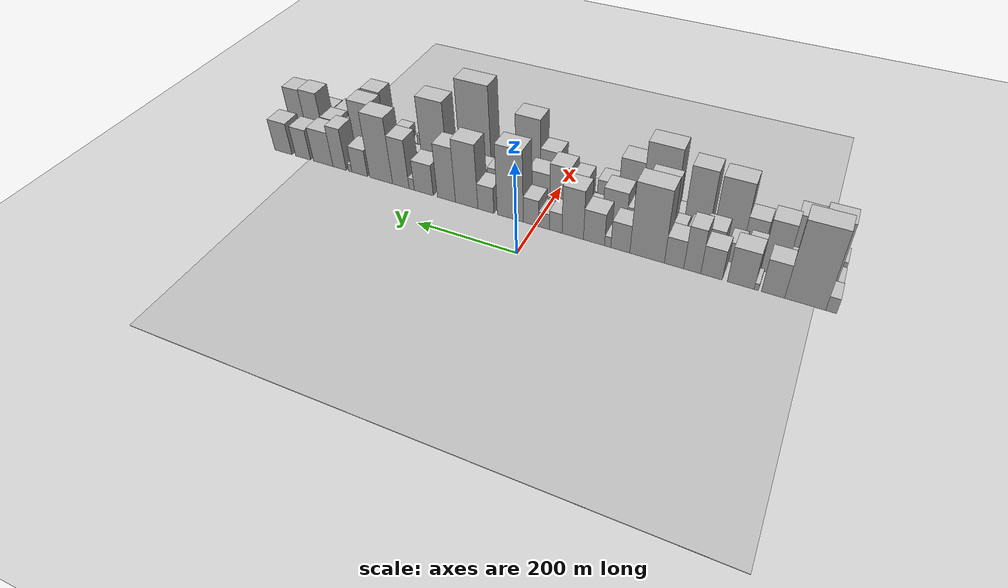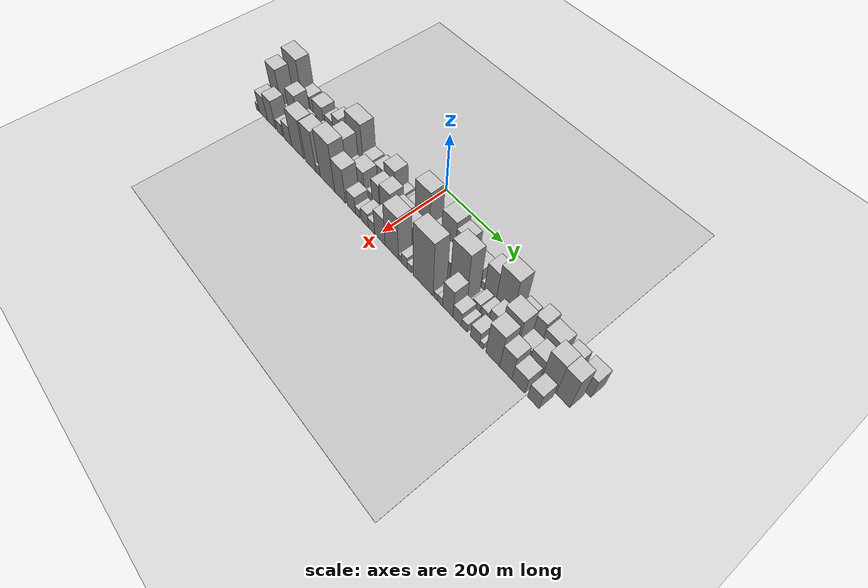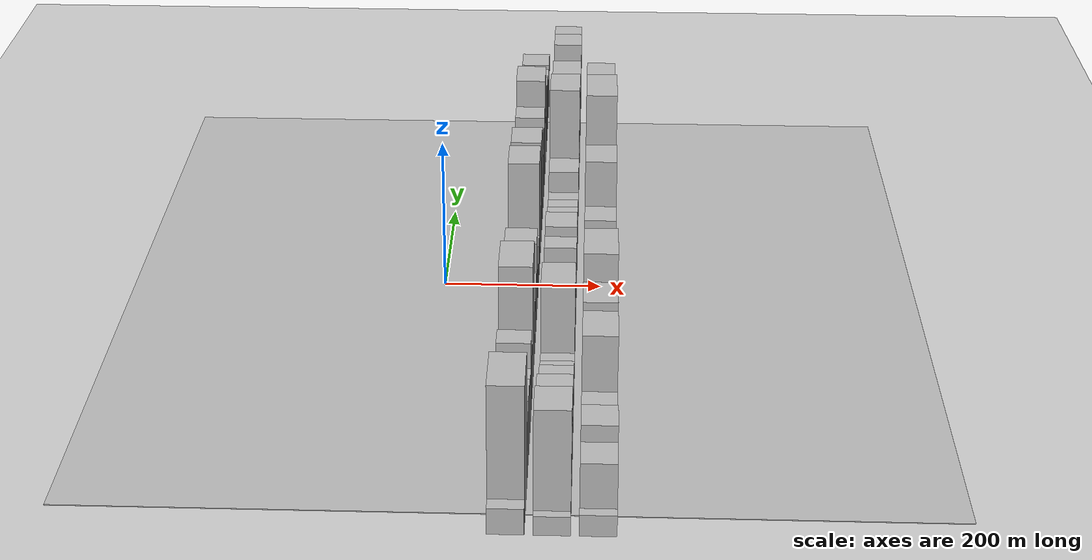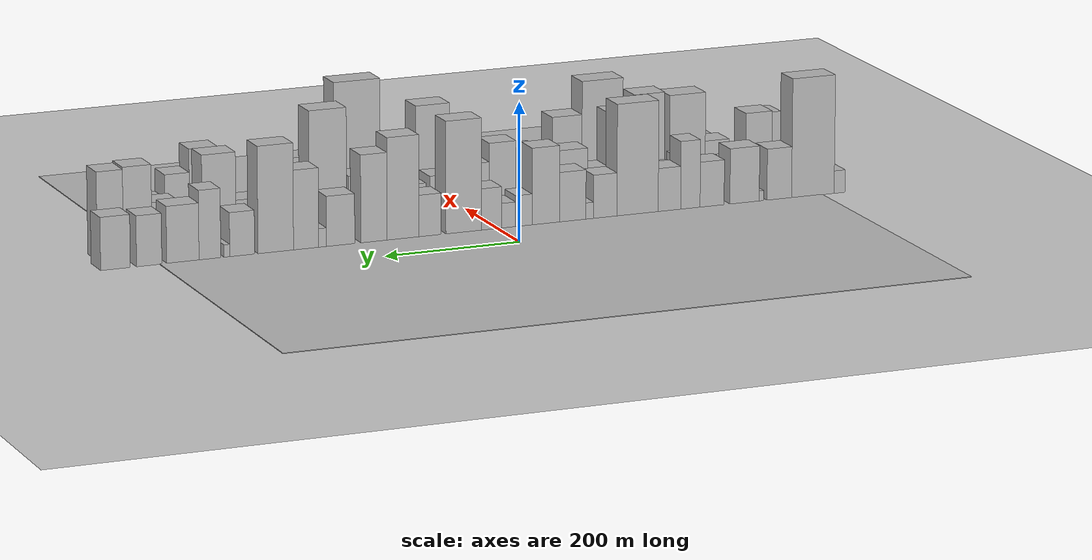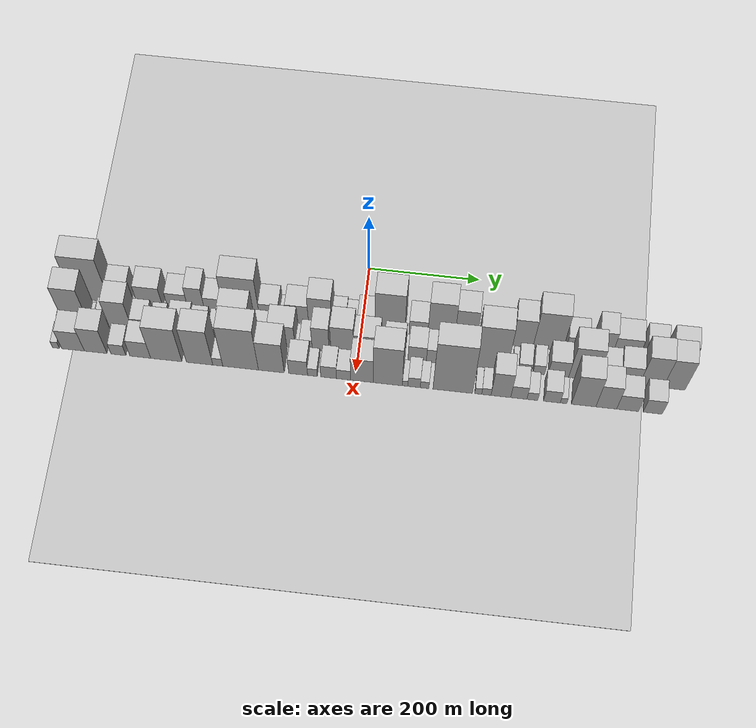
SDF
<?xml version="1.0" encoding="utf-8"?>

<sdf version="1.6">

   <world name="default">

      <gui fullscreen="0">

         <camera name="user_camera">

            <pose>-15 0 4.57585 0 0 0</pose>

            <view_controller>orbit</view_controller>

         </camera>

      </gui>

      <scene>

         <sky>

           <clouds>

             <speed>12</speed>

           </clouds>

         </sky>

         <ambient>0.4 0.4 0.4 1</ambient>

         <background>0.7 0.7 0.7 1</background>

         <shadows>1</shadows>

      </scene>

      <gravity>0 0 -9.8066</gravity>

      <magnetic_field>6e-06 2.3e-05 -4.2e-05</magnetic_field>

      <physics default="0" name="default_physics" type="ode">

         <ode>

            <solver>

               <type>quick</type>

               <iters>10</iters>

               <sor>1.0</sor>

               <use_dynamic_moi_rescaling>0</use_dynamic_moi_rescaling>

            </solver>

            <constraints>

               <cfm>0</cfm>

               <erp>0.2</erp>

               <contact_max_correcting_vel>100</contact_max_correcting_vel>

               <contact_surface_layer>0.001</contact_surface_layer>

            </constraints>

         </ode>

         <max_step_size>0.004</max_step_size>

         <real_time_factor>1</real_time_factor>

         <real_time_update_rate>250</real_time_update_rate>

      </physics>

      <light name="sun" type="directional">

         <cast_shadows>1</cast_shadows>

         <pose>0 0 10 0 0 0</pose>

         <diffuse>0.8 0.8 0.8 1</diffuse>

         <specular>0.2 0.2 0.2 1</specular>

         <attenuation>

            <range>1000</range>

            <constant>0.9</constant>

            <linear>0.01</linear>

            <quadratic>0.001</quadratic>

         </attenuation>

         <direction>-0.5 0.1 -0.9</direction>

      </light>

      <include>

         <name>ground_plane_1</name>

         <uri>model://HANNAS_ground_plane</uri>

         <pose>0 0 0  0 0 0</pose>

      </include>

      <include>

         <name>ground_plane_2</name>

         <uri>model://HANNAS_ground_plane</uri>

         <pose>100 0 0  0 0 0</pose>

      </include>

      <model name="building_1">

         <static>1</static>

         <pose frame="">100.0000 -527.2603 0 0.000000 0.000000 0.000000</pose>

         <link name="link">

            <pose frame="">0 0 16.50 0 0 0</pose>

            <collision name="collision">

               <geometry>

                  <box>

                     <size>40.0000 17.4794 33.0000</size>

                  </box>

               </geometry>

               <max_contacts>10</max_contacts>

               <surface>

                  <contact>

                     <ode/>

                  </contact>

                  <bounce/>

                  <friction>

                     <torsional>

                        <ode/>

                     </torsional>

                     <ode/>

                  </friction>

               </surface>

            </collision>

            <visual name="visual">

               <cast_shadows>0</cast_shadows>

               <geometry>

                  <box>

                     <size>40.0000 17.4794 33.0000</size>

                  </box>

               </geometry>

               <material>

                  <script>

                     <uri>model://HANNAS_wall/materials/scripts</uri>

                     <uri>model://HANNAS_wall/materials/textures</uri>

                     <name>vrc/HANNAS_wall</name>

                  </script>

               </material>

            </visual>

            <self_collide>0</self_collide>

            <enable_wind>0</enable_wind>

            <kinematic>0</kinematic>

         </link>

      </model>

      <model name="building_2">

         <static>1</static>

         <pose frame="">100.0000 -485.1375 0 0.000000 0.000000 0.000000</pose>

         <link name="link">

            <pose frame="">0 0 87.00 0 0 0</pose>

            <collision name="collision">

               <geometry>

                  <box>

                     <size>40.0000 66.7662 174.0000</size>

                  </box>

               </geometry>

               <max_contacts>10</max_contacts>

               <surface>

                  <contact>

                     <ode/>

                  </contact>

                  <bounce/>

                  <friction>

                     <torsional>

                        <ode/>

                     </torsional>

                     <ode/>

                  </friction>

               </surface>

            </collision>

            <visual name="visual">

               <cast_shadows>0</cast_shadows>

               <geometry>

                  <box>

                     <size>40.0000 66.7662 174.0000</size>

                  </box>

               </geometry>

               <material>

                  <script>

                     <uri>model://HANNAS_wall/materials/scripts</uri>

                     <uri>model://HANNAS_wall/materials/textures</uri>

                     <name>vrc/HANNAS_wall</name>

                  </script>

               </material>

            </visual>

            <self_collide>0</self_collide>

            <enable_wind>0</enable_wind>

            <kinematic>0</kinematic>

         </link>

      </model>

      <model name="building_3">

         <static>1</static>

         <pose frame="">100.0000 -432.5556 0 0.000000 0.000000 0.000000</pose>

         <link name="link">

            <pose frame="">0 0 37.50 0 0 0</pose>

            <collision name="collision">

               <geometry>

                  <box>

                     <size>40.0000 38.3976 75.0000</size>

                  </box>

               </geometry>

               <max_contacts>10</max_contacts>

               <surface>

                  <contact>

                     <ode/>

                  </contact>

                  <bounce/>

                  <friction>

                     <torsional>

                        <ode/>

                     </torsional>

                     <ode/>

                  </friction>

               </surface>

            </collision>

            <visual name="visual">

               <cast_shadows>0</cast_shadows>

               <geometry>

                  <box>

                     <size>40.0000 38.3976 75.0000</size>

                  </box>

               </geometry>

               <material>

                  <script>

                     <uri>model://HANNAS_wall/materials/scripts</uri>

                     <uri>model://HANNAS_wall/materials/textures</uri>

                     <name>vrc/HANNAS_wall</name>

                  </script>

               </material>

            </visual>

            <self_collide>0</self_collide>

            <enable_wind>0</enable_wind>

            <kinematic>0</kinematic>

         </link>

      </model>

      <model name="building_4">

         <static>1</static>

         <pose frame="">100.0000 -404.8420 0 0.000000 0.000000 0.000000</pose>

         <link name="link">

            <pose frame="">0 0 7.50 0 0 0</pose>

            <collision name="collision">

               <geometry>

                  <box>

                     <size>40.0000 7.0295 15.0000</size>

                  </box>

               </geometry>

               <max_contacts>10</max_contacts>

               <surface>

                  <contact>

                     <ode/>

                  </contact>

                  <bounce/>

                  <friction>

                     <torsional>

                        <ode/>

                     </torsional>

                     <ode/>

                  </friction>

               </surface>

            </collision>

            <visual name="visual">

               <cast_shadows>0</cast_shadows>

               <geometry>

                  <box>

                     <size>40.0000 7.0295 15.0000</size>

                  </box>

               </geometry>

               <material>

                  <script>

                     <uri>model://HANNAS_wall/materials/scripts</uri>

                     <uri>model://HANNAS_wall/materials/textures</uri>

                     <name>vrc/HANNAS_wall</name>

                  </script>

               </material>

            </visual>

            <self_collide>0</self_collide>

            <enable_wind>0</enable_wind>

            <kinematic>0</kinematic>

         </link>

      </model>

      <model name="building_5">

         <static>1</static>

         <pose frame="">100.0000 -378.5148 0 0.000000 0.000000 0.000000</pose>

         <link name="link">

            <pose frame="">0 0 40.50 0 0 0</pose>

            <collision name="collision">

               <geometry>

                  <box>

                     <size>40.0000 45.6248 81.0000</size>

                  </box>

               </geometry>

               <max_contacts>10</max_contacts>

               <surface>

                  <contact>

                     <ode/>

                  </contact>

                  <bounce/>

                  <friction>

                     <torsional>

                        <ode/>

                     </torsional>

                     <ode/>

                  </friction>

               </surface>

            </collision>

            <visual name="visual">

               <cast_shadows>0</cast_shadows>

               <geometry>

                  <box>

                     <size>40.0000 45.6248 81.0000</size>

                  </box>

               </geometry>

               <material>

                  <script>

                     <uri>model://HANNAS_wall/materials/scripts</uri>

                     <uri>model://HANNAS_wall/materials/textures</uri>

                     <name>vrc/HANNAS_wall</name>

                  </script>

               </material>

            </visual>

            <self_collide>0</self_collide>

            <enable_wind>0</enable_wind>

            <kinematic>0</kinematic>

         </link>

      </model>

      <model name="building_6">

         <static>1</static>

         <pose frame="">100.0000 -328.0879 0 0.000000 0.000000 0.000000</pose>

         <link name="link">

            <pose frame="">0 0 33.00 0 0 0</pose>

            <collision name="collision">

               <geometry>

                  <box>

                     <size>40.0000 37.2291 66.0000</size>

                  </box>

               </geometry>

               <max_contacts>10</max_contacts>

               <surface>

                  <contact>

                     <ode/>

                  </contact>

                  <bounce/>

                  <friction>

                     <torsional>

                        <ode/>

                     </torsional>

                     <ode/>

                  </friction>

               </surface>

            </collision>

            <visual name="visual">

               <cast_shadows>0</cast_shadows>

               <geometry>

                  <box>

                     <size>40.0000 37.2291 66.0000</size>

                  </box>

               </geometry>

               <material>

                  <script>

                     <uri>model://HANNAS_wall/materials/scripts</uri>

                     <uri>model://HANNAS_wall/materials/textures</uri>

                     <name>vrc/HANNAS_wall</name>

                  </script>

               </material>

            </visual>

            <self_collide>0</self_collide>

            <enable_wind>0</enable_wind>

            <kinematic>0</kinematic>

         </link>

      </model>

      <model name="building_7">

         <static>1</static>

         <pose frame="">100.0000 -294.4978 0 0.000000 0.000000 0.000000</pose>

         <link name="link">

            <pose frame="">0 0 49.50 0 0 0</pose>

            <collision name="collision">

               <geometry>

                  <box>

                     <size>40.0000 29.9511 99.0000</size>

                  </box>

               </geometry>

               <max_contacts>10</max_contacts>

               <surface>

                  <contact>

                     <ode/>

                  </contact>

                  <bounce/>

                  <friction>

                     <torsional>

                        <ode/>

                     </torsional>

                     <ode/>

                  </friction>

               </surface>

            </collision>

            <visual name="visual">

               <cast_shadows>0</cast_shadows>

               <geometry>

                  <box>

                     <size>40.0000 29.9511 99.0000</size>

                  </box>

               </geometry>

               <material>

                  <script>

                     <uri>model://HANNAS_wall/materials/scripts</uri>

                     <uri>model://HANNAS_wall/materials/textures</uri>

                     <name>vrc/HANNAS_wall</name>

                  </script>

               </material>

            </visual>

            <self_collide>0</self_collide>

            <enable_wind>0</enable_wind>

            <kinematic>0</kinematic>

         </link>

      </model>

      <model name="building_8">

         <static>1</static>

         <pose frame="">100.0000 -262.1933 0 0.000000 0.000000 0.000000</pose>

         <link name="link">

            <pose frame="">0 0 31.50 0 0 0</pose>

            <collision name="collision">

               <geometry>

                  <box>

                     <size>40.0000 34.6579 63.0000</size>

                  </box>

               </geometry>

               <max_contacts>10</max_contacts>

               <surface>

                  <contact>

                     <ode/>

                  </contact>

                  <bounce/>

                  <friction>

                     <torsional>

                        <ode/>

                     </torsional>

                     <ode/>

                  </friction>

               </surface>

            </collision>

            <visual name="visual">

               <cast_shadows>0</cast_shadows>

               <geometry>

                  <box>

                     <size>40.0000 34.6579 63.0000</size>

                  </box>

               </geometry>

               <material>

                  <script>

                     <uri>model://HANNAS_wall/materials/scripts</uri>

                     <uri>model://HANNAS_wall/materials/textures</uri>

                     <name>vrc/HANNAS_wall</name>

                  </script>

               </material>

            </visual>

            <self_collide>0</self_collide>

            <enable_wind>0</enable_wind>

            <kinematic>0</kinematic>

         </link>

      </model>

      <model name="building_9">

         <static>1</static>

         <pose frame="">100.0000 -213.1922 0 0.000000 0.000000 0.000000</pose>

         <link name="link">

            <pose frame="">0 0 81.00 0 0 0</pose>

            <collision name="collision">

               <geometry>

                  <box>

                     <size>40.0000 63.3443 162.0000</size>

                  </box>

               </geometry>

               <max_contacts>10</max_contacts>

               <surface>

                  <contact>

                     <ode/>

                  </contact>

                  <bounce/>

                  <friction>

                     <torsional>

                        <ode/>

                     </torsional>

                     <ode/>

                  </friction>

               </surface>

            </collision>

            <visual name="visual">

               <cast_shadows>0</cast_shadows>

               <geometry>

                  <box>

                     <size>40.0000 63.3443 162.0000</size>

                  </box>

               </geometry>

               <material>

                  <script>

                     <uri>model://HANNAS_wall/materials/scripts</uri>

                     <uri>model://HANNAS_wall/materials/textures</uri>

                     <name>vrc/HANNAS_wall</name>

                  </script>

               </material>

            </visual>

            <self_collide>0</self_collide>

            <enable_wind>0</enable_wind>

            <kinematic>0</kinematic>

         </link>

      </model>

      <model name="building_10">

         <static>1</static>

         <pose frame="">100.0000 -163.7489 0 0.000000 0.000000 0.000000</pose>

         <link name="link">

            <pose frame="">0 0 31.50 0 0 0</pose>

            <collision name="collision">

               <geometry>

                  <box>

                     <size>40.0000 35.5423 63.0000</size>

                  </box>

               </geometry>

               <max_contacts>10</max_contacts>

               <surface>

                  <contact>

                     <ode/>

                  </contact>

                  <bounce/>

                  <friction>

                     <torsional>

                        <ode/>

                     </torsional>

                     <ode/>

                  </friction>

               </surface>

            </collision>

            <visual name="visual">

               <cast_shadows>0</cast_shadows>

               <geometry>

                  <box>

                     <size>40.0000 35.5423 63.0000</size>

                  </box>

               </geometry>

               <material>

                  <script>

                     <uri>model://HANNAS_wall/materials/scripts</uri>

                     <uri>model://HANNAS_wall/materials/textures</uri>

                     <name>vrc/HANNAS_wall</name>

                  </script>

               </material>

            </visual>

            <self_collide>0</self_collide>

            <enable_wind>0</enable_wind>

            <kinematic>0</kinematic>

         </link>

      </model>

      <model name="building_11">

         <static>1</static>

         <pose frame="">100.0000 -140.0537 0 0.000000 0.000000 0.000000</pose>

         <link name="link">

            <pose frame="">0 0 12.00 0 0 0</pose>

            <collision name="collision">

               <geometry>

                  <box>

                     <size>40.0000 11.8480 24.0000</size>

                  </box>

               </geometry>

               <max_contacts>10</max_contacts>

               <surface>

                  <contact>

                     <ode/>

                  </contact>

                  <bounce/>

                  <friction>

                     <torsional>

                        <ode/>

                     </torsional>

                     <ode/>

                  </friction>

               </surface>

            </collision>

            <visual name="visual">

               <cast_shadows>0</cast_shadows>

               <geometry>

                  <box>

                     <size>40.0000 11.8480 24.0000</size>

                  </box>

               </geometry>

               <material>

                  <script>

                     <uri>model://HANNAS_wall/materials/scripts</uri>

                     <uri>model://HANNAS_wall/materials/textures</uri>

                     <name>vrc/HANNAS_wall</name>

                  </script>

               </material>

            </visual>

            <self_collide>0</self_collide>

            <enable_wind>0</enable_wind>

            <kinematic>0</kinematic>

         </link>

      </model>

      <model name="building_12">

         <static>1</static>

         <pose frame="">100.0000 -114.0702 0 0.000000 0.000000 0.000000</pose>

         <link name="link">

            <pose frame="">0 0 36.00 0 0 0</pose>

            <collision name="collision">

               <geometry>

                  <box>

                     <size>40.0000 40.1191 72.0000</size>

                  </box>

               </geometry>

               <max_contacts>10</max_contacts>

               <surface>

                  <contact>

                     <ode/>

                  </contact>

                  <bounce/>

                  <friction>

                     <torsional>

                        <ode/>

                     </torsional>

                     <ode/>

                  </friction>

               </surface>

            </collision>

            <visual name="visual">

               <cast_shadows>0</cast_shadows>

               <geometry>

                  <box>

                     <size>40.0000 40.1191 72.0000</size>

                  </box>

               </geometry>

               <material>

                  <script>

                     <uri>model://HANNAS_wall/materials/scripts</uri>

                     <uri>model://HANNAS_wall/materials/textures</uri>

                     <name>vrc/HANNAS_wall</name>

                  </script>

               </material>

            </visual>

            <self_collide>0</self_collide>

            <enable_wind>0</enable_wind>

            <kinematic>0</kinematic>

         </link>

      </model>

      <model name="building_13">

         <static>1</static>

         <pose frame="">100.0000 -73.1719 0 0.000000 0.000000 0.000000</pose>

         <link name="link">

            <pose frame="">0 0 55.50 0 0 0</pose>

            <collision name="collision">

               <geometry>

                  <box>

                     <size>40.0000 41.6777 111.0000</size>

                  </box>

               </geometry>

               <max_contacts>10</max_contacts>

               <surface>

                  <contact>

                     <ode/>

                  </contact>

                  <bounce/>

                  <friction>

                     <torsional>

                        <ode/>

                     </torsional>

                     <ode/>

                  </friction>

               </surface>

            </collision>

            <visual name="visual">

               <cast_shadows>0</cast_shadows>

               <geometry>

                  <box>

                     <size>40.0000 41.6777 111.0000</size>

                  </box>

               </geometry>

               <material>

                  <script>

                     <uri>model://HANNAS_wall/materials/scripts</uri>

                     <uri>model://HANNAS_wall/materials/textures</uri>

                     <name>vrc/HANNAS_wall</name>

                  </script>

               </material>

            </visual>

            <self_collide>0</self_collide>

            <enable_wind>0</enable_wind>

            <kinematic>0</kinematic>

         </link>

      </model>

      <model name="building_14">

         <static>1</static>

         <pose frame="">100.0000 -39.7930 0 0.000000 0.000000 0.000000</pose>

         <link name="link">

            <pose frame="">0 0 22.50 0 0 0</pose>

            <collision name="collision">

               <geometry>

                  <box>

                     <size>40.0000 25.0800 45.0000</size>

                  </box>

               </geometry>

               <max_contacts>10</max_contacts>

               <surface>

                  <contact>

                     <ode/>

                  </contact>

                  <bounce/>

                  <friction>

                     <torsional>

                        <ode/>

                     </torsional>

                     <ode/>

                  </friction>

               </surface>

            </collision>

            <visual name="visual">

               <cast_shadows>0</cast_shadows>

               <geometry>

                  <box>

                     <size>40.0000 25.0800 45.0000</size>

                  </box>

               </geometry>

               <material>

                  <script>

                     <uri>model://HANNAS_wall/materials/scripts</uri>

                     <uri>model://HANNAS_wall/materials/textures</uri>

                     <name>vrc/HANNAS_wall</name>

                  </script>

               </material>

            </visual>

            <self_collide>0</self_collide>

            <enable_wind>0</enable_wind>

            <kinematic>0</kinematic>

         </link>

      </model>

      <model name="building_15">

         <static>1</static>

         <pose frame="">100.0000 -16.8667 0 0.000000 0.000000 0.000000</pose>

         <link name="link">

            <pose frame="">0 0 18.00 0 0 0</pose>

            <collision name="collision">

               <geometry>

                  <box>

                     <size>40.0000 20.7725 36.0000</size>

                  </box>

               </geometry>

               <max_contacts>10</max_contacts>

               <surface>

                  <contact>

                     <ode/>

                  </contact>

                  <bounce/>

                  <friction>

                     <torsional>

                        <ode/>

                     </torsional>

                     <ode/>

                  </friction>

               </surface>

            </collision>

            <visual name="visual">

               <cast_shadows>0</cast_shadows>

               <geometry>

                  <box>

                     <size>40.0000 20.7725 36.0000</size>

                  </box>

               </geometry>

               <material>

                  <script>

                     <uri>model://HANNAS_wall/materials/scripts</uri>

                     <uri>model://HANNAS_wall/materials/textures</uri>

                     <name>vrc/HANNAS_wall</name>

                  </script>

               </material>

            </visual>

            <self_collide>0</self_collide>

            <enable_wind>0</enable_wind>

            <kinematic>0</kinematic>

         </link>

      </model>

      <model name="building_16">

         <static>1</static>

         <pose frame="">100.0000 9.0122 0 0.000000 0.000000 0.000000</pose>

         <link name="link">

            <pose frame="">0 0 30.00 0 0 0</pose>

            <collision name="collision">

               <geometry>

                  <box>

                     <size>40.0000 30.9853 60.0000</size>

                  </box>

               </geometry>

               <max_contacts>10</max_contacts>

               <surface>

                  <contact>

                     <ode/>

                  </contact>

                  <bounce/>

                  <friction>

                     <torsional>

                        <ode/>

                     </torsional>

                     <ode/>

                  </friction>

               </surface>

            </collision>

            <visual name="visual">

               <cast_shadows>0</cast_shadows>

               <geometry>

                  <box>

                     <size>40.0000 30.9853 60.0000</size>

                  </box>

               </geometry>

               <material>

                  <script>

                     <uri>model://HANNAS_wall/materials/scripts</uri>

                     <uri>model://HANNAS_wall/materials/textures</uri>

                     <name>vrc/HANNAS_wall</name>

                  </script>

               </material>

            </visual>

            <self_collide>0</self_collide>

            <enable_wind>0</enable_wind>

            <kinematic>0</kinematic>

         </link>

      </model>

      <model name="building_17">

         <static>1</static>

         <pose frame="">100.0000 51.1494 0 0.000000 0.000000 0.000000</pose>

         <link name="link">

            <pose frame="">0 0 81.00 0 0 0</pose>

            <collision name="collision">

               <geometry>

                  <box>

                     <size>40.0000 53.2891 162.0000</size>

                  </box>

               </geometry>

               <max_contacts>10</max_contacts>

               <surface>

                  <contact>

                     <ode/>

                  </contact>

                  <bounce/>

                  <friction>

                     <torsional>

                        <ode/>

                     </torsional>

                     <ode/>

                  </friction>

               </surface>

            </collision>

            <visual name="visual">

               <cast_shadows>0</cast_shadows>

               <geometry>

                  <box>

                     <size>40.0000 53.2891 162.0000</size>

                  </box>

               </geometry>

               <material>

                  <script>

                     <uri>model://HANNAS_wall/materials/scripts</uri>

                     <uri>model://HANNAS_wall/materials/textures</uri>

                     <name>vrc/HANNAS_wall</name>

                  </script>

               </material>

            </visual>

            <self_collide>0</self_collide>

            <enable_wind>0</enable_wind>

            <kinematic>0</kinematic>

         </link>

      </model>

      <model name="building_18">

         <static>1</static>

         <pose frame="">100.0000 101.5394 0 0.000000 0.000000 0.000000</pose>

         <link name="link">

            <pose frame="">0 0 30.00 0 0 0</pose>

            <collision name="collision">

               <geometry>

                  <box>

                     <size>40.0000 33.4910 60.0000</size>

                  </box>

               </geometry>

               <max_contacts>10</max_contacts>

               <surface>

                  <contact>

                     <ode/>

                  </contact>

                  <bounce/>

                  <friction>

                     <torsional>

                        <ode/>

                     </torsional>

                     <ode/>

                  </friction>

               </surface>

            </collision>

            <visual name="visual">

               <cast_shadows>0</cast_shadows>

               <geometry>

                  <box>

                     <size>40.0000 33.4910 60.0000</size>

                  </box>

               </geometry>

               <material>

                  <script>

                     <uri>model://HANNAS_wall/materials/scripts</uri>

                     <uri>model://HANNAS_wall/materials/textures</uri>

                     <name>vrc/HANNAS_wall</name>

                  </script>

               </material>

            </visual>

            <self_collide>0</self_collide>

            <enable_wind>0</enable_wind>

            <kinematic>0</kinematic>

         </link>

      </model>

      <model name="building_19">

         <static>1</static>

         <pose frame="">100.0000 142.0829 0 0.000000 0.000000 0.000000</pose>

         <link name="link">

            <pose frame="">0 0 73.50 0 0 0</pose>

            <collision name="collision">

               <geometry>

                  <box>

                     <size>40.0000 47.5960 147.0000</size>

                  </box>

               </geometry>

               <max_contacts>10</max_contacts>

               <surface>

                  <contact>

                     <ode/>

                  </contact>

                  <bounce/>

                  <friction>

                     <torsional>

                        <ode/>

                     </torsional>

                     <ode/>

                  </friction>

               </surface>

            </collision>

            <visual name="visual">

               <cast_shadows>0</cast_shadows>

               <geometry>

                  <box>

                     <size>40.0000 47.5960 147.0000</size>

                  </box>

               </geometry>

               <material>

                  <script>

                     <uri>model://HANNAS_wall/materials/scripts</uri>

                     <uri>model://HANNAS_wall/materials/textures</uri>

                     <name>vrc/HANNAS_wall</name>

                  </script>

               </material>

            </visual>

            <self_collide>0</self_collide>

            <enable_wind>0</enable_wind>

            <kinematic>0</kinematic>

         </link>

      </model>

      <model name="building_20">

         <static>1</static>

         <pose frame="">100.0000 185.3595 0 0.000000 0.000000 0.000000</pose>

         <link name="link">

            <pose frame="">0 0 63.00 0 0 0</pose>

            <collision name="collision">

               <geometry>

                  <box>

                     <size>40.0000 38.9573 126.0000</size>

                  </box>

               </geometry>

               <max_contacts>10</max_contacts>

               <surface>

                  <contact>

                     <ode/>

                  </contact>

                  <bounce/>

                  <friction>

                     <torsional>

                        <ode/>

                     </torsional>

                     <ode/>

                  </friction>

               </surface>

            </collision>

            <visual name="visual">

               <cast_shadows>0</cast_shadows>

               <geometry>

                  <box>

                     <size>40.0000 38.9573 126.0000</size>

                  </box>

               </geometry>

               <material>

                  <script>

                     <uri>model://HANNAS_wall/materials/scripts</uri>

                     <uri>model://HANNAS_wall/materials/textures</uri>

                     <name>vrc/HANNAS_wall</name>

                  </script>

               </material>

            </visual>

            <self_collide>0</self_collide>

            <enable_wind>0</enable_wind>

            <kinematic>0</kinematic>

         </link>

      </model>

      <model name="building_21">

         <static>1</static>

         <pose frame="">100.0000 234.8111 0 0.000000 0.000000 0.000000</pose>

         <link name="link">

            <pose frame="">0 0 36.00 0 0 0</pose>

            <collision name="collision">

               <geometry>

                  <box>

                     <size>40.0000 41.9458 72.0000</size>

                  </box>

               </geometry>

               <max_contacts>10</max_contacts>

               <surface>

                  <contact>

                     <ode/>

                  </contact>

                  <bounce/>

                  <friction>

                     <torsional>

                        <ode/>

                     </torsional>

                     <ode/>

                  </friction>

               </surface>

            </collision>

            <visual name="visual">

               <cast_shadows>0</cast_shadows>

               <geometry>

                  <box>

                     <size>40.0000 41.9458 72.0000</size>

                  </box>

               </geometry>

               <material>

                  <script>

                     <uri>model://HANNAS_wall/materials/scripts</uri>

                     <uri>model://HANNAS_wall/materials/textures</uri>

                     <name>vrc/HANNAS_wall</name>

                  </script>

               </material>

            </visual>

            <self_collide>0</self_collide>

            <enable_wind>0</enable_wind>

            <kinematic>0</kinematic>

         </link>

      </model>

      <model name="building_22">

         <static>1</static>

         <pose frame="">100.0000 261.5546 0 0.000000 0.000000 0.000000</pose>

         <link name="link">

            <pose frame="">0 0 13.50 0 0 0</pose>

            <collision name="collision">

               <geometry>

                  <box>

                     <size>40.0000 11.5412 27.0000</size>

                  </box>

               </geometry>

               <max_contacts>10</max_contacts>

               <surface>

                  <contact>

                     <ode/>

                  </contact>

                  <bounce/>

                  <friction>

                     <torsional>

                        <ode/>

                     </torsional>

                     <ode/>

                  </friction>

               </surface>

            </collision>

            <visual name="visual">

               <cast_shadows>0</cast_shadows>

               <geometry>

                  <box>

                     <size>40.0000 11.5412 27.0000</size>

                  </box>

               </geometry>

               <material>

                  <script>

                     <uri>model://HANNAS_wall/materials/scripts</uri>

                     <uri>model://HANNAS_wall/materials/textures</uri>

                     <name>vrc/HANNAS_wall</name>

                  </script>

               </material>

            </visual>

            <self_collide>0</self_collide>

            <enable_wind>0</enable_wind>

            <kinematic>0</kinematic>

         </link>

      </model>

      <model name="building_23">

         <static>1</static>

         <pose frame="">100.0000 285.8989 0 0.000000 0.000000 0.000000</pose>

         <link name="link">

            <pose frame="">0 0 57.00 0 0 0</pose>

            <collision name="collision">

               <geometry>

                  <box>

                     <size>40.0000 37.1474 114.0000</size>

                  </box>

               </geometry>

               <max_contacts>10</max_contacts>

               <surface>

                  <contact>

                     <ode/>

                  </contact>

                  <bounce/>

                  <friction>

                     <torsional>

                        <ode/>

                     </torsional>

                     <ode/>

                  </friction>

               </surface>

            </collision>

            <visual name="visual">

               <cast_shadows>0</cast_shadows>

               <geometry>

                  <box>

                     <size>40.0000 37.1474 114.0000</size>

                  </box>

               </geometry>

               <material>

                  <script>

                     <uri>model://HANNAS_wall/materials/scripts</uri>

                     <uri>model://HANNAS_wall/materials/textures</uri>

                     <name>vrc/HANNAS_wall</name>

                  </script>

               </material>

            </visual>

            <self_collide>0</self_collide>

            <enable_wind>0</enable_wind>

            <kinematic>0</kinematic>

         </link>

      </model>

      <model name="building_24">

         <static>1</static>

         <pose frame="">100.0000 330.6133 0 0.000000 0.000000 0.000000</pose>

         <link name="link">

            <pose frame="">0 0 76.50 0 0 0</pose>

            <collision name="collision">

               <geometry>

                  <box>

                     <size>40.0000 52.2815 153.0000</size>

                  </box>

               </geometry>

               <max_contacts>10</max_contacts>

               <surface>

                  <contact>

                     <ode/>

                  </contact>

                  <bounce/>

                  <friction>

                     <torsional>

                        <ode/>

                     </torsional>

                     <ode/>

                  </friction>

               </surface>

            </collision>

            <visual name="visual">

               <cast_shadows>0</cast_shadows>

               <geometry>

                  <box>

                     <size>40.0000 52.2815 153.0000</size>

                  </box>

               </geometry>

               <material>

                  <script>

                     <uri>model://HANNAS_wall/materials/scripts</uri>

                     <uri>model://HANNAS_wall/materials/textures</uri>

                     <name>vrc/HANNAS_wall</name>

                  </script>

               </material>

            </visual>

            <self_collide>0</self_collide>

            <enable_wind>0</enable_wind>

            <kinematic>0</kinematic>

         </link>

      </model>

      <model name="building_25">

         <static>1</static>

         <pose frame="">100.0000 379.9582 0 0.000000 0.000000 0.000000</pose>

         <link name="link">

            <pose frame="">0 0 31.50 0 0 0</pose>

            <collision name="collision">

               <geometry>

                  <box>

                     <size>40.0000 36.4083 63.0000</size>

                  </box>

               </geometry>

               <max_contacts>10</max_contacts>

               <surface>

                  <contact>

                     <ode/>

                  </contact>

                  <bounce/>

                  <friction>

                     <torsional>

                        <ode/>

                     </torsional>

                     <ode/>

                  </friction>

               </surface>

            </collision>

            <visual name="visual">

               <cast_shadows>0</cast_shadows>

               <geometry>

                  <box>

                     <size>40.0000 36.4083 63.0000</size>

                  </box>

               </geometry>

               <material>

                  <script>

                     <uri>model://HANNAS_wall/materials/scripts</uri>

                     <uri>model://HANNAS_wall/materials/textures</uri>

                     <name>vrc/HANNAS_wall</name>

                  </script>

               </material>

            </visual>

            <self_collide>0</self_collide>

            <enable_wind>0</enable_wind>

            <kinematic>0</kinematic>

         </link>

      </model>

      <model name="building_26">

         <static>1</static>

         <pose frame="">100.0000 402.2550 0 0.000000 0.000000 0.000000</pose>

         <link name="link">

            <pose frame="">0 0 9.00 0 0 0</pose>

            <collision name="collision">

               <geometry>

                  <box>

                     <size>40.0000 8.1853 18.0000</size>

                  </box>

               </geometry>

               <max_contacts>10</max_contacts>

               <surface>

                  <contact>

                     <ode/>

                  </contact>

                  <bounce/>

                  <friction>

                     <torsional>

                        <ode/>

                     </torsional>

                     <ode/>

                  </friction>

               </surface>

            </collision>

            <visual name="visual">

               <cast_shadows>0</cast_shadows>

               <geometry>

                  <box>

                     <size>40.0000 8.1853 18.0000</size>

                  </box>

               </geometry>

               <material>

                  <script>

                     <uri>model://HANNAS_wall/materials/scripts</uri>

                     <uri>model://HANNAS_wall/materials/textures</uri>

                     <name>vrc/HANNAS_wall</name>

                  </script>

               </material>

            </visual>

            <self_collide>0</self_collide>

            <enable_wind>0</enable_wind>

            <kinematic>0</kinematic>

         </link>

      </model>

      <model name="building_27">

         <static>1</static>

         <pose frame="">100.0000 427.1888 0 0.000000 0.000000 0.000000</pose>

         <link name="link">

            <pose frame="">0 0 49.50 0 0 0</pose>

            <collision name="collision">

               <geometry>

                  <box>

                     <size>40.0000 31.6823 99.0000</size>

                  </box>

               </geometry>

               <max_contacts>10</max_contacts>

               <surface>

                  <contact>

                     <ode/>

                  </contact>

                  <bounce/>

                  <friction>

                     <torsional>

                        <ode/>

                     </torsional>

                     <ode/>

                  </friction>

               </surface>

            </collision>

            <visual name="visual">

               <cast_shadows>0</cast_shadows>

               <geometry>

                  <box>

                     <size>40.0000 31.6823 99.0000</size>

                  </box>

               </geometry>

               <material>

                  <script>

                     <uri>model://HANNAS_wall/materials/scripts</uri>

                     <uri>model://HANNAS_wall/materials/textures</uri>

                     <name>vrc/HANNAS_wall</name>

                  </script>

               </material>

            </visual>

            <self_collide>0</self_collide>

            <enable_wind>0</enable_wind>

            <kinematic>0</kinematic>

         </link>

      </model>

      <model name="building_28">

         <static>1</static>

         <pose frame="">100.0000 466.5669 0 0.000000 0.000000 0.000000</pose>

         <link name="link">

            <pose frame="">0 0 40.50 0 0 0</pose>

            <collision name="collision">

               <geometry>

                  <box>

                     <size>40.0000 47.0739 81.0000</size>

                  </box>

               </geometry>

               <max_contacts>10</max_contacts>

               <surface>

                  <contact>

                     <ode/>

                  </contact>

                  <bounce/>

                  <friction>

                     <torsional>

                        <ode/>

                     </torsional>

                     <ode/>

                  </friction>

               </surface>

            </collision>

            <visual name="visual">

               <cast_shadows>0</cast_shadows>

               <geometry>

                  <box>

                     <size>40.0000 47.0739 81.0000</size>

                  </box>

               </geometry>

               <material>

                  <script>

                     <uri>model://HANNAS_wall/materials/scripts</uri>

                     <uri>model://HANNAS_wall/materials/textures</uri>

                     <name>vrc/HANNAS_wall</name>

                  </script>

               </material>

            </visual>

            <self_collide>0</self_collide>

            <enable_wind>0</enable_wind>

            <kinematic>0</kinematic>

         </link>

      </model>

      <model name="building_29">

         <static>1</static>

         <pose frame="">100.0000 515.4584 0 0.000000 0.000000 0.000000</pose>

         <link name="link">

            <pose frame="">0 0 36.00 0 0 0</pose>

            <collision name="collision">

               <geometry>

                  <box>

                     <size>40.0000 36.7091 72.0000</size>

                  </box>

               </geometry>

               <max_contacts>10</max_contacts>

               <surface>

                  <contact>

                     <ode/>

                  </contact>

                  <bounce/>

                  <friction>

                     <torsional>

                        <ode/>

                     </torsional>

                     <ode/>

                  </friction>

               </surface>

            </collision>

            <visual name="visual">

               <cast_shadows>0</cast_shadows>

               <geometry>

                  <box>

                     <size>40.0000 36.7091 72.0000</size>

                  </box>

               </geometry>

               <material>

                  <script>

                     <uri>model://HANNAS_wall/materials/scripts</uri>

                     <uri>model://HANNAS_wall/materials/textures</uri>

                     <name>vrc/HANNAS_wall</name>

                  </script>

               </material>

            </visual>

            <self_collide>0</self_collide>

            <enable_wind>0</enable_wind>

            <kinematic>0</kinematic>

         </link>

      </model>

      <model name="building_30">

         <static>1</static>

         <pose frame="">100.0000 564.2426 0 0.000000 0.000000 0.000000</pose>

         <link name="link">

            <pose frame="">0 0 37.50 0 0 0</pose>

            <collision name="collision">

               <geometry>

                  <box>

                     <size>40.0000 42.8594 75.0000</size>

                  </box>

               </geometry>

               <max_contacts>10</max_contacts>

               <surface>

                  <contact>

                     <ode/>

                  </contact>

                  <bounce/>

                  <friction>

                     <torsional>

                        <ode/>

                     </torsional>

                     <ode/>

                  </friction>

               </surface>

            </collision>

            <visual name="visual">

               <cast_shadows>0</cast_shadows>

               <geometry>

                  <box>

                     <size>40.0000 42.8594 75.0000</size>

                  </box>

               </geometry>

               <material>

                  <script>

                     <uri>model://HANNAS_wall/materials/scripts</uri>

                     <uri>model://HANNAS_wall/materials/textures</uri>

                     <name>vrc/HANNAS_wall</name>

                  </script>

               </material>

            </visual>

            <self_collide>0</self_collide>

            <enable_wind>0</enable_wind>

            <kinematic>0</kinematic>

         </link>

      </model>

      <model name="building_31">

         <static>1</static>

         <pose frame="">149.0000 -530.6760 0 0.000000 0.000000 0.000000</pose>

         <link name="link">

            <pose frame="">0 0 12.00 0 0 0</pose>

            <collision name="collision">

               <geometry>

                  <box>

                     <size>40.0000 10.6480 24.0000</size>

                  </box>

               </geometry>

               <max_contacts>10</max_contacts>

               <surface>

                  <contact>

                     <ode/>

                  </contact>

                  <bounce/>

                  <friction>

                     <torsional>

                        <ode/>

                     </torsional>

                     <ode/>

                  </friction>

               </surface>

            </collision>

            <visual name="visual">

               <cast_shadows>0</cast_shadows>

               <geometry>

                  <box>

                     <size>40.0000 10.6480 24.0000</size>

                  </box>

               </geometry>

               <material>

                  <script>

                     <uri>model://HANNAS_wall/materials/scripts</uri>

                     <uri>model://HANNAS_wall/materials/textures</uri>

                     <name>vrc/HANNAS_wall</name>

                  </script>

               </material>

            </visual>

            <self_collide>0</self_collide>

            <enable_wind>0</enable_wind>

            <kinematic>0</kinematic>

         </link>

      </model>

      <model name="building_32">

         <static>1</static>

         <pose frame="">149.0000 -502.1637 0 0.000000 0.000000 0.000000</pose>

         <link name="link">

            <pose frame="">0 0 75.00 0 0 0</pose>

            <collision name="collision">

               <geometry>

                  <box>

                     <size>40.0000 46.3765 150.0000</size>

                  </box>

               </geometry>

               <max_contacts>10</max_contacts>

               <surface>

                  <contact>

                     <ode/>

                  </contact>

                  <bounce/>

                  <friction>

                     <torsional>

                        <ode/>

                     </torsional>

                     <ode/>

                  </friction>

               </surface>

            </collision>

            <visual name="visual">

               <cast_shadows>0</cast_shadows>

               <geometry>

                  <box>

                     <size>40.0000 46.3765 150.0000</size>

                  </box>

               </geometry>

               <material>

                  <script>

                     <uri>model://HANNAS_wall/materials/scripts</uri>

                     <uri>model://HANNAS_wall/materials/textures</uri>

                     <name>vrc/HANNAS_wall</name>

                  </script>

               </material>

            </visual>

            <self_collide>0</self_collide>

            <enable_wind>0</enable_wind>

            <kinematic>0</kinematic>

         </link>

      </model>

      <model name="building_33">

         <static>1</static>

         <pose frame="">149.0000 -475.7980 0 0.000000 0.000000 0.000000</pose>

         <link name="link">

            <pose frame="">0 0 7.50 0 0 0</pose>

            <collision name="collision">

               <geometry>

                  <box>

                     <size>40.0000 6.3549 15.0000</size>

                  </box>

               </geometry>

               <max_contacts>10</max_contacts>

               <surface>

                  <contact>

                     <ode/>

                  </contact>

                  <bounce/>

                  <friction>

                     <torsional>

                        <ode/>

                     </torsional>

                     <ode/>

                  </friction>

               </surface>

            </collision>

            <visual name="visual">

               <cast_shadows>0</cast_shadows>

               <geometry>

                  <box>

                     <size>40.0000 6.3549 15.0000</size>

                  </box>

               </geometry>

               <material>

                  <script>

                     <uri>model://HANNAS_wall/materials/scripts</uri>

                     <uri>model://HANNAS_wall/materials/textures</uri>

                     <name>vrc/HANNAS_wall</name>

                  </script>

               </material>

            </visual>

            <self_collide>0</self_collide>

            <enable_wind>0</enable_wind>

            <kinematic>0</kinematic>

         </link>

      </model>

      <model name="building_34">

         <static>1</static>

         <pose frame="">149.0000 -469.1543 0 0.000000 0.000000 0.000000</pose>

         <link name="link">

            <pose frame="">0 0 7.50 0 0 0</pose>

            <collision name="collision">

               <geometry>

                  <box>

                     <size>40.0000 6.9325 15.0000</size>

                  </box>

               </geometry>

               <max_contacts>10</max_contacts>

               <surface>

                  <contact>

                     <ode/>

                  </contact>

                  <bounce/>

                  <friction>

                     <torsional>

                        <ode/>

                     </torsional>

                     <ode/>

                  </friction>

               </surface>

            </collision>

            <visual name="visual">

               <cast_shadows>0</cast_shadows>

               <geometry>

                  <box>

                     <size>40.0000 6.9325 15.0000</size>

                  </box>

               </geometry>

               <material>

                  <script>

                     <uri>model://HANNAS_wall/materials/scripts</uri>

                     <uri>model://HANNAS_wall/materials/textures</uri>

                     <name>vrc/HANNAS_wall</name>

                  </script>

               </material>

            </visual>

            <self_collide>0</self_collide>

            <enable_wind>0</enable_wind>

            <kinematic>0</kinematic>

         </link>

      </model>

      <model name="building_35">

         <static>1</static>

         <pose frame="">149.0000 -454.3602 0 0.000000 0.000000 0.000000</pose>

         <link name="link">

            <pose frame="">0 0 19.50 0 0 0</pose>

            <collision name="collision">

               <geometry>

                  <box>

                     <size>40.0000 22.6557 39.0000</size>

                  </box>

               </geometry>

               <max_contacts>10</max_contacts>

               <surface>

                  <contact>

                     <ode/>

                  </contact>

                  <bounce/>

                  <friction>

                     <torsional>

                        <ode/>

                     </torsional>

                     <ode/>

                  </friction>

               </surface>

            </collision>

            <visual name="visual">

               <cast_shadows>0</cast_shadows>

               <geometry>

                  <box>

                     <size>40.0000 22.6557 39.0000</size>

                  </box>

               </geometry>

               <material>

                  <script>

                     <uri>model://HANNAS_wall/materials/scripts</uri>

                     <uri>model://HANNAS_wall/materials/textures</uri>

                     <name>vrc/HANNAS_wall</name>

                  </script>

               </material>

            </visual>

            <self_collide>0</self_collide>

            <enable_wind>0</enable_wind>

            <kinematic>0</kinematic>

         </link>

      </model>

      <model name="building_36">

         <static>1</static>

         <pose frame="">149.0000 -422.4298 0 0.000000 0.000000 0.000000</pose>

         <link name="link">

            <pose frame="">0 0 58.50 0 0 0</pose>

            <collision name="collision">

               <geometry>

                  <box>

                     <size>40.0000 41.2049 117.0000</size>

                  </box>

               </geometry>

               <max_contacts>10</max_contacts>

               <surface>

                  <contact>

                     <ode/>

                  </contact>

                  <bounce/>

                  <friction>

                     <torsional>

                        <ode/>

                     </torsional>

                     <ode/>

                  </friction>

               </surface>

            </collision>

            <visual name="visual">

               <cast_shadows>0</cast_shadows>

               <geometry>

                  <box>

                     <size>40.0000 41.2049 117.0000</size>

                  </box>

               </geometry>

               <material>

                  <script>

                     <uri>model://HANNAS_wall/materials/scripts</uri>

                     <uri>model://HANNAS_wall/materials/textures</uri>

                     <name>vrc/HANNAS_wall</name>

                  </script>

               </material>

            </visual>

            <self_collide>0</self_collide>

            <enable_wind>0</enable_wind>

            <kinematic>0</kinematic>

         </link>

      </model>

      <model name="building_37">

         <static>1</static>

         <pose frame="">149.0000 -386.6518 0 0.000000 0.000000 0.000000</pose>

         <link name="link">

            <pose frame="">0 0 25.50 0 0 0</pose>

            <collision name="collision">

               <geometry>

                  <box>

                     <size>40.0000 30.3512 51.0000</size>

                  </box>

               </geometry>

               <max_contacts>10</max_contacts>

               <surface>

                  <contact>

                     <ode/>

                  </contact>

                  <bounce/>

                  <friction>

                     <torsional>

                        <ode/>

                     </torsional>

                     <ode/>

                  </friction>

               </surface>

            </collision>

            <visual name="visual">

               <cast_shadows>0</cast_shadows>

               <geometry>

                  <box>

                     <size>40.0000 30.3512 51.0000</size>

                  </box>

               </geometry>

               <material>

                  <script>

                     <uri>model://HANNAS_wall/materials/scripts</uri>

                     <uri>model://HANNAS_wall/materials/textures</uri>

                     <name>vrc/HANNAS_wall</name>

                  </script>

               </material>

            </visual>

            <self_collide>0</self_collide>

            <enable_wind>0</enable_wind>

            <kinematic>0</kinematic>

         </link>

      </model>

      <model name="building_38">

         <static>1</static>

         <pose frame="">149.0000 -353.5843 0 0.000000 0.000000 0.000000</pose>

         <link name="link">

            <pose frame="">0 0 22.50 0 0 0</pose>

            <collision name="collision">

               <geometry>

                  <box>

                     <size>40.0000 25.7837 45.0000</size>

                  </box>

               </geometry>

               <max_contacts>10</max_contacts>

               <surface>

                  <contact>

                     <ode/>

                  </contact>

                  <bounce/>

                  <friction>

                     <torsional>

                        <ode/>

                     </torsional>

                     <ode/>

                  </friction>

               </surface>

            </collision>

            <visual name="visual">

               <cast_shadows>0</cast_shadows>

               <geometry>

                  <box>

                     <size>40.0000 25.7837 45.0000</size>

                  </box>

               </geometry>

               <material>

                  <script>

                     <uri>model://HANNAS_wall/materials/scripts</uri>

                     <uri>model://HANNAS_wall/materials/textures</uri>

                     <name>vrc/HANNAS_wall</name>

                  </script>

               </material>

            </visual>

            <self_collide>0</self_collide>

            <enable_wind>0</enable_wind>

            <kinematic>0</kinematic>

         </link>

      </model>

      <model name="building_39">

         <static>1</static>

         <pose frame="">149.0000 -314.9544 0 0.000000 0.000000 0.000000</pose>

         <link name="link">

            <pose frame="">0 0 31.50 0 0 0</pose>

            <collision name="collision">

               <geometry>

                  <box>

                     <size>40.0000 37.4761 63.0000</size>

                  </box>

               </geometry>

               <max_contacts>10</max_contacts>

               <surface>

                  <contact>

                     <ode/>

                  </contact>

                  <bounce/>

                  <friction>

                     <torsional>

                        <ode/>

                     </torsional>

                     <ode/>

                  </friction>

               </surface>

            </collision>

            <visual name="visual">

               <cast_shadows>0</cast_shadows>

               <geometry>

                  <box>

                     <size>40.0000 37.4761 63.0000</size>

                  </box>

               </geometry>

               <material>

                  <script>

                     <uri>model://HANNAS_wall/materials/scripts</uri>

                     <uri>model://HANNAS_wall/materials/textures</uri>

                     <name>vrc/HANNAS_wall</name>

                  </script>

               </material>

            </visual>

            <self_collide>0</self_collide>

            <enable_wind>0</enable_wind>

            <kinematic>0</kinematic>

         </link>

      </model>

      <model name="building_40">

         <static>1</static>

         <pose frame="">149.0000 -281.8113 0 0.000000 0.000000 0.000000</pose>

         <link name="link">

            <pose frame="">0 0 25.50 0 0 0</pose>

            <collision name="collision">

               <geometry>

                  <box>

                     <size>40.0000 28.8101 51.0000</size>

                  </box>

               </geometry>

               <max_contacts>10</max_contacts>

               <surface>

                  <contact>

                     <ode/>

                  </contact>

                  <bounce/>

                  <friction>

                     <torsional>

                        <ode/>

                     </torsional>

                     <ode/>

                  </friction>

               </surface>

            </collision>

            <visual name="visual">

               <cast_shadows>0</cast_shadows>

               <geometry>

                  <box>

                     <size>40.0000 28.8101 51.0000</size>

                  </box>

               </geometry>

               <material>

                  <script>

                     <uri>model://HANNAS_wall/materials/scripts</uri>

                     <uri>model://HANNAS_wall/materials/textures</uri>

                     <name>vrc/HANNAS_wall</name>

                  </script>

               </material>

            </visual>

            <self_collide>0</self_collide>

            <enable_wind>0</enable_wind>

            <kinematic>0</kinematic>

         </link>

      </model>

      <model name="building_41">

         <static>1</static>

         <pose frame="">149.0000 -251.8208 0 0.000000 0.000000 0.000000</pose>

         <link name="link">

            <pose frame="">0 0 22.50 0 0 0</pose>

            <collision name="collision">

               <geometry>

                  <box>

                     <size>40.0000 23.1710 45.0000</size>

                  </box>

               </geometry>

               <max_contacts>10</max_contacts>

               <surface>

                  <contact>

                     <ode/>

                  </contact>

                  <bounce/>

                  <friction>

                     <torsional>

                        <ode/>

                     </torsional>

                     <ode/>

                  </friction>

               </surface>

            </collision>

            <visual name="visual">

               <cast_shadows>0</cast_shadows>

               <geometry>

                  <box>

                     <size>40.0000 23.1710 45.0000</size>

                  </box>

               </geometry>

               <material>

                  <script>

                     <uri>model://HANNAS_wall/materials/scripts</uri>

                     <uri>model://HANNAS_wall/materials/textures</uri>

                     <name>vrc/HANNAS_wall</name>

                  </script>

               </material>

            </visual>

            <self_collide>0</self_collide>

            <enable_wind>0</enable_wind>

            <kinematic>0</kinematic>

         </link>

      </model>

      <model name="building_42">

         <static>1</static>

         <pose frame="">149.0000 -214.3614 0 0.000000 0.000000 0.000000</pose>

         <link name="link">

            <pose frame="">0 0 69.00 0 0 0</pose>

            <collision name="collision">

               <geometry>

                  <box>

                     <size>40.0000 51.7477 138.0000</size>

                  </box>

               </geometry>

               <max_contacts>10</max_contacts>

               <surface>

                  <contact>

                     <ode/>

                  </contact>

                  <bounce/>

                  <friction>

                     <torsional>

                        <ode/>

                     </torsional>

                     <ode/>

                  </friction>

               </surface>

            </collision>

            <visual name="visual">

               <cast_shadows>0</cast_shadows>

               <geometry>

                  <box>

                     <size>40.0000 51.7477 138.0000</size>

                  </box>

               </geometry>

               <material>

                  <script>

                     <uri>model://HANNAS_wall/materials/scripts</uri>

                     <uri>model://HANNAS_wall/materials/textures</uri>

                     <name>vrc/HANNAS_wall</name>

                  </script>

               </material>

            </visual>

            <self_collide>0</self_collide>

            <enable_wind>0</enable_wind>

            <kinematic>0</kinematic>

         </link>

      </model>

      <model name="building_43">

         <static>1</static>

         <pose frame="">149.0000 -172.9483 0 0.000000 0.000000 0.000000</pose>

         <link name="link">

            <pose frame="">0 0 30.00 0 0 0</pose>

            <collision name="collision">

               <geometry>

                  <box>

                     <size>40.0000 31.0785 60.0000</size>

                  </box>

               </geometry>

               <max_contacts>10</max_contacts>

               <surface>

                  <contact>

                     <ode/>

                  </contact>

                  <bounce/>

                  <friction>

                     <torsional>

                        <ode/>

                     </torsional>

                     <ode/>

                  </friction>

               </surface>

            </collision>

            <visual name="visual">

               <cast_shadows>0</cast_shadows>

               <geometry>

                  <box>

                     <size>40.0000 31.0785 60.0000</size>

                  </box>

               </geometry>

               <material>

                  <script>

                     <uri>model://HANNAS_wall/materials/scripts</uri>

                     <uri>model://HANNAS_wall/materials/textures</uri>

                     <name>vrc/HANNAS_wall</name>

                  </script>

               </material>

            </visual>

            <self_collide>0</self_collide>

            <enable_wind>0</enable_wind>

            <kinematic>0</kinematic>

         </link>

      </model>

      <model name="building_44">

         <static>1</static>

         <pose frame="">149.0000 -134.3167 0 0.000000 0.000000 0.000000</pose>

         <link name="link">

            <pose frame="">0 0 45.00 0 0 0</pose>

            <collision name="collision">

               <geometry>

                  <box>

                     <size>40.0000 46.1847 90.0000</size>

                  </box>

               </geometry>

               <max_contacts>10</max_contacts>

               <surface>

                  <contact>

                     <ode/>

                  </contact>

                  <bounce/>

                  <friction>

                     <torsional>

                        <ode/>

                     </torsional>

                     <ode/>

                  </friction>

               </surface>

            </collision>

            <visual name="visual">

               <cast_shadows>0</cast_shadows>

               <geometry>

                  <box>

                     <size>40.0000 46.1847 90.0000</size>

                  </box>

               </geometry>

               <material>

                  <script>

                     <uri>model://HANNAS_wall/materials/scripts</uri>

                     <uri>model://HANNAS_wall/materials/textures</uri>

                     <name>vrc/HANNAS_wall</name>

                  </script>

               </material>

            </visual>

            <self_collide>0</self_collide>

            <enable_wind>0</enable_wind>

            <kinematic>0</kinematic>

         </link>

      </model>

      <model name="building_45">

         <static>1</static>

         <pose frame="">149.0000 -107.1081 0 0.000000 0.000000 0.000000</pose>

         <link name="link">

            <pose frame="">0 0 9.00 0 0 0</pose>

            <collision name="collision">

               <geometry>

                  <box>

                     <size>40.0000 8.2325 18.0000</size>

                  </box>

               </geometry>

               <max_contacts>10</max_contacts>

               <surface>

                  <contact>

                     <ode/>

                  </contact>

                  <bounce/>

                  <friction>

                     <torsional>

                        <ode/>

                     </torsional>

                     <ode/>

                  </friction>

               </surface>

            </collision>

            <visual name="visual">

               <cast_shadows>0</cast_shadows>

               <geometry>

                  <box>

                     <size>40.0000 8.2325 18.0000</size>

                  </box>

               </geometry>

               <material>

                  <script>

                     <uri>model://HANNAS_wall/materials/scripts</uri>

                     <uri>model://HANNAS_wall/materials/textures</uri>

                     <name>vrc/HANNAS_wall</name>

                  </script>

               </material>

            </visual>

            <self_collide>0</self_collide>

            <enable_wind>0</enable_wind>

            <kinematic>0</kinematic>

         </link>

      </model>

      <model name="building_46">

         <static>1</static>

         <pose frame="">149.0000 -91.9620 0 0.000000 0.000000 0.000000</pose>

         <link name="link">

            <pose frame="">0 0 19.50 0 0 0</pose>

            <collision name="collision">

               <geometry>

                  <box>

                     <size>40.0000 22.0598 39.0000</size>

                  </box>

               </geometry>

               <max_contacts>10</max_contacts>

               <surface>

                  <contact>

                     <ode/>

                  </contact>

                  <bounce/>

                  <friction>

                     <torsional>

                        <ode/>

                     </torsional>

                     <ode/>

                  </friction>

               </surface>

            </collision>

            <visual name="visual">

               <cast_shadows>0</cast_shadows>

               <geometry>

                  <box>

                     <size>40.0000 22.0598 39.0000</size>

                  </box>

               </geometry>

               <material>

                  <script>

                     <uri>model://HANNAS_wall/materials/scripts</uri>

                     <uri>model://HANNAS_wall/materials/textures</uri>

                     <name>vrc/HANNAS_wall</name>

                  </script>

               </material>

            </visual>

            <self_collide>0</self_collide>

            <enable_wind>0</enable_wind>

            <kinematic>0</kinematic>

         </link>

      </model>

      <model name="building_47">

         <static>1</static>

         <pose frame="">149.0000 -65.8754 0 0.000000 0.000000 0.000000</pose>

         <link name="link">

            <pose frame="">0 0 49.50 0 0 0</pose>

            <collision name="collision">

               <geometry>

                  <box>

                     <size>40.0000 30.1134 99.0000</size>

                  </box>

               </geometry>

               <max_contacts>10</max_contacts>

               <surface>

                  <contact>

                     <ode/>

                  </contact>

                  <bounce/>

                  <friction>

                     <torsional>

                        <ode/>

                     </torsional>

                     <ode/>

                  </friction>

               </surface>

            </collision>

            <visual name="visual">

               <cast_shadows>0</cast_shadows>

               <geometry>

                  <box>

                     <size>40.0000 30.1134 99.0000</size>

                  </box>

               </geometry>

               <material>

                  <script>

                     <uri>model://HANNAS_wall/materials/scripts</uri>

                     <uri>model://HANNAS_wall/materials/textures</uri>

                     <name>vrc/HANNAS_wall</name>

                  </script>

               </material>

            </visual>

            <self_collide>0</self_collide>

            <enable_wind>0</enable_wind>

            <kinematic>0</kinematic>

         </link>

      </model>

      <model name="building_48">

         <static>1</static>

         <pose frame="">149.0000 -27.6340 0 0.000000 0.000000 0.000000</pose>

         <link name="link">

            <pose frame="">0 0 55.50 0 0 0</pose>

            <collision name="collision">

               <geometry>

                  <box>

                     <size>40.0000 40.3695 111.0000</size>

                  </box>

               </geometry>

               <max_contacts>10</max_contacts>

               <surface>

                  <contact>

                     <ode/>

                  </contact>

                  <bounce/>

                  <friction>

                     <torsional>

                        <ode/>

                     </torsional>

                     <ode/>

                  </friction>

               </surface>

            </collision>

            <visual name="visual">

               <cast_shadows>0</cast_shadows>

               <geometry>

                  <box>

                     <size>40.0000 40.3695 111.0000</size>

                  </box>

               </geometry>

               <material>

                  <script>

                     <uri>model://HANNAS_wall/materials/scripts</uri>

                     <uri>model://HANNAS_wall/materials/textures</uri>

                     <name>vrc/HANNAS_wall</name>

                  </script>

               </material>

            </visual>

            <self_collide>0</self_collide>

            <enable_wind>0</enable_wind>

            <kinematic>0</kinematic>

         </link>

      </model>

      <model name="building_49">

         <static>1</static>

         <pose frame="">149.0000 15.2305 0 0.000000 0.000000 0.000000</pose>

         <link name="link">

            <pose frame="">0 0 42.00 0 0 0</pose>

            <collision name="collision">

               <geometry>

                  <box>

                     <size>40.0000 45.3596 84.0000</size>

                  </box>

               </geometry>

               <max_contacts>10</max_contacts>

               <surface>

                  <contact>

                     <ode/>

                  </contact>

                  <bounce/>

                  <friction>

                     <torsional>

                        <ode/>

                     </torsional>

                     <ode/>

                  </friction>

               </surface>

            </collision>

            <visual name="visual">

               <cast_shadows>0</cast_shadows>

               <geometry>

                  <box>

                     <size>40.0000 45.3596 84.0000</size>

                  </box>

               </geometry>

               <material>

                  <script>

                     <uri>model://HANNAS_wall/materials/scripts</uri>

                     <uri>model://HANNAS_wall/materials/textures</uri>

                     <name>vrc/HANNAS_wall</name>

                  </script>

               </material>

            </visual>

            <self_collide>0</self_collide>

            <enable_wind>0</enable_wind>

            <kinematic>0</kinematic>

         </link>

      </model>

      <model name="building_50">

         <static>1</static>

         <pose frame="">149.0000 41.6079 0 0.000000 0.000000 0.000000</pose>

         <link name="link">

            <pose frame="">0 0 9.00 0 0 0</pose>

            <collision name="collision">

               <geometry>

                  <box>

                     <size>40.0000 7.3952 18.0000</size>

                  </box>

               </geometry>

               <max_contacts>10</max_contacts>

               <surface>

                  <contact>

                     <ode/>

                  </contact>

                  <bounce/>

                  <friction>

                     <torsional>

                        <ode/>

                     </torsional>

                     <ode/>

                  </friction>

               </surface>

            </collision>

            <visual name="visual">

               <cast_shadows>0</cast_shadows>

               <geometry>

                  <box>

                     <size>40.0000 7.3952 18.0000</size>

                  </box>

               </geometry>

               <material>

                  <script>

                     <uri>model://HANNAS_wall/materials/scripts</uri>

                     <uri>model://HANNAS_wall/materials/textures</uri>

                     <name>vrc/HANNAS_wall</name>

                  </script>

               </material>

            </visual>

            <self_collide>0</self_collide>

            <enable_wind>0</enable_wind>

            <kinematic>0</kinematic>

         </link>

      </model>

      <model name="building_51">

         <static>1</static>

         <pose frame="">149.0000 63.8269 0 0.000000 0.000000 0.000000</pose>

         <link name="link">

            <pose frame="">0 0 36.00 0 0 0</pose>

            <collision name="collision">

               <geometry>

                  <box>

                     <size>40.0000 37.0427 72.0000</size>

                  </box>

               </geometry>

               <max_contacts>10</max_contacts>

               <surface>

                  <contact>

                     <ode/>

                  </contact>

                  <bounce/>

                  <friction>

                     <torsional>

                        <ode/>

                     </torsional>

                     <ode/>

                  </friction>

               </surface>

            </collision>

            <visual name="visual">

               <cast_shadows>0</cast_shadows>

               <geometry>

                  <box>

                     <size>40.0000 37.0427 72.0000</size>

                  </box>

               </geometry>

               <material>

                  <script>

                     <uri>model://HANNAS_wall/materials/scripts</uri>

                     <uri>model://HANNAS_wall/materials/textures</uri>

                     <name>vrc/HANNAS_wall</name>

                  </script>

               </material>

            </visual>

            <self_collide>0</self_collide>

            <enable_wind>0</enable_wind>

            <kinematic>0</kinematic>

         </link>

      </model>

      <model name="building_52">

         <static>1</static>

         <pose frame="">149.0000 104.5426 0 0.000000 0.000000 0.000000</pose>

         <link name="link">

            <pose frame="">0 0 31.50 0 0 0</pose>

            <collision name="collision">

               <geometry>

                  <box>

                     <size>40.0000 32.3889 63.0000</size>

                  </box>

               </geometry>

               <max_contacts>10</max_contacts>

               <surface>

                  <contact>

                     <ode/>

                  </contact>

                  <bounce/>

                  <friction>

                     <torsional>

                        <ode/>

                     </torsional>

                     <ode/>

                  </friction>

               </surface>

            </collision>

            <visual name="visual">

               <cast_shadows>0</cast_shadows>

               <geometry>

                  <box>

                     <size>40.0000 32.3889 63.0000</size>

                  </box>

               </geometry>

               <material>

                  <script>

                     <uri>model://HANNAS_wall/materials/scripts</uri>

                     <uri>model://HANNAS_wall/materials/textures</uri>

                     <name>vrc/HANNAS_wall</name>

                  </script>

               </material>

            </visual>

            <self_collide>0</self_collide>

            <enable_wind>0</enable_wind>

            <kinematic>0</kinematic>

         </link>

      </model>

      <model name="building_53">

         <static>1</static>

         <pose frame="">149.0000 137.4647 0 0.000000 0.000000 0.000000</pose>

         <link name="link">

            <pose frame="">0 0 28.50 0 0 0</pose>

            <collision name="collision">

               <geometry>

                  <box>

                     <size>40.0000 33.4552 57.0000</size>

                  </box>

               </geometry>

               <max_contacts>10</max_contacts>

               <surface>

                  <contact>

                     <ode/>

                  </contact>

                  <bounce/>

                  <friction>

                     <torsional>

                        <ode/>

                     </torsional>

                     <ode/>

                  </friction>

               </surface>

            </collision>

            <visual name="visual">

               <cast_shadows>0</cast_shadows>

               <geometry>

                  <box>

                     <size>40.0000 33.4552 57.0000</size>

                  </box>

               </geometry>

               <material>

                  <script>

                     <uri>model://HANNAS_wall/materials/scripts</uri>

                     <uri>model://HANNAS_wall/materials/textures</uri>

                     <name>vrc/HANNAS_wall</name>

                  </script>

               </material>

            </visual>

            <self_collide>0</self_collide>

            <enable_wind>0</enable_wind>

            <kinematic>0</kinematic>

         </link>

      </model>

      <model name="building_54">

         <static>1</static>

         <pose frame="">149.0000 157.3524 0 0.000000 0.000000 0.000000</pose>

         <link name="link">

            <pose frame="">0 0 7.50 0 0 0</pose>

            <collision name="collision">

               <geometry>

                  <box>

                     <size>40.0000 6.3202 15.0000</size>

                  </box>

               </geometry>

               <max_contacts>10</max_contacts>

               <surface>

                  <contact>

                     <ode/>

                  </contact>

                  <bounce/>

                  <friction>

                     <torsional>

                        <ode/>

                     </torsional>

                     <ode/>

                  </friction>

               </surface>

            </collision>

            <visual name="visual">

               <cast_shadows>0</cast_shadows>

               <geometry>

                  <box>

                     <size>40.0000 6.3202 15.0000</size>

                  </box>

               </geometry>

               <material>

                  <script>

                     <uri>model://HANNAS_wall/materials/scripts</uri>

                     <uri>model://HANNAS_wall/materials/textures</uri>

                     <name>vrc/HANNAS_wall</name>

                  </script>

               </material>

            </visual>

            <self_collide>0</self_collide>

            <enable_wind>0</enable_wind>

            <kinematic>0</kinematic>

         </link>

      </model>

      <model name="building_55">

         <static>1</static>

         <pose frame="">149.0000 182.1373 0 0.000000 0.000000 0.000000</pose>

         <link name="link">

            <pose frame="">0 0 42.00 0 0 0</pose>

            <collision name="collision">

               <geometry>

                  <box>

                     <size>40.0000 43.2496 84.0000</size>

                  </box>

               </geometry>

               <max_contacts>10</max_contacts>

               <surface>

                  <contact>

                     <ode/>

                  </contact>

                  <bounce/>

                  <friction>

                     <torsional>

                        <ode/>

                     </torsional>

                     <ode/>

                  </friction>

               </surface>

            </collision>

            <visual name="visual">

               <cast_shadows>0</cast_shadows>

               <geometry>

                  <box>

                     <size>40.0000 43.2496 84.0000</size>

                  </box>

               </geometry>

               <material>

                  <script>

                     <uri>model://HANNAS_wall/materials/scripts</uri>

                     <uri>model://HANNAS_wall/materials/textures</uri>

                     <name>vrc/HANNAS_wall</name>

                  </script>

               </material>

            </visual>

            <self_collide>0</self_collide>

            <enable_wind>0</enable_wind>

            <kinematic>0</kinematic>

         </link>

      </model>

      <model name="building_56">

         <static>1</static>

         <pose frame="">149.0000 234.6852 0 0.000000 0.000000 0.000000</pose>

         <link name="link">

            <pose frame="">0 0 91.50 0 0 0</pose>

            <collision name="collision">

               <geometry>

                  <box>

                     <size>40.0000 55.8464 183.0000</size>

                  </box>

               </geometry>

               <max_contacts>10</max_contacts>

               <surface>

                  <contact>

                     <ode/>

                  </contact>

                  <bounce/>

                  <friction>

                     <torsional>

                        <ode/>

                     </torsional>

                     <ode/>

                  </friction>

               </surface>

            </collision>

            <visual name="visual">

               <cast_shadows>0</cast_shadows>

               <geometry>

                  <box>

                     <size>40.0000 55.8464 183.0000</size>

                  </box>

               </geometry>

               <material>

                  <script>

                     <uri>model://HANNAS_wall/materials/scripts</uri>

                     <uri>model://HANNAS_wall/materials/textures</uri>

                     <name>vrc/HANNAS_wall</name>

                  </script>

               </material>

            </visual>

            <self_collide>0</self_collide>

            <enable_wind>0</enable_wind>

            <kinematic>0</kinematic>

         </link>

      </model>

      <model name="building_57">

         <static>1</static>

         <pose frame="">149.0000 276.7256 0 0.000000 0.000000 0.000000</pose>

         <link name="link">

            <pose frame="">0 0 10.50 0 0 0</pose>

            <collision name="collision">

               <geometry>

                  <box>

                     <size>40.0000 10.2343 21.0000</size>

                  </box>

               </geometry>

               <max_contacts>10</max_contacts>

               <surface>

                  <contact>

                     <ode/>

                  </contact>

                  <bounce/>

                  <friction>

                     <torsional>

                        <ode/>

                     </torsional>

                     <ode/>

                  </friction>

               </surface>

            </collision>

            <visual name="visual">

               <cast_shadows>0</cast_shadows>

               <geometry>

                  <box>

                     <size>40.0000 10.2343 21.0000</size>

                  </box>

               </geometry>

               <material>

                  <script>

                     <uri>model://HANNAS_wall/materials/scripts</uri>

                     <uri>model://HANNAS_wall/materials/textures</uri>

                     <name>vrc/HANNAS_wall</name>

                  </script>

               </material>

            </visual>

            <self_collide>0</self_collide>

            <enable_wind>0</enable_wind>

            <kinematic>0</kinematic>

         </link>

      </model>

      <model name="building_58">

         <static>1</static>

         <pose frame="">149.0000 293.4140 0 0.000000 0.000000 0.000000</pose>

         <link name="link">

            <pose frame="">0 0 19.50 0 0 0</pose>

            <collision name="collision">

               <geometry>

                  <box>

                     <size>40.0000 23.1425 39.0000</size>

                  </box>

               </geometry>

               <max_contacts>10</max_contacts>

               <surface>

                  <contact>

                     <ode/>

                  </contact>

                  <bounce/>

                  <friction>

                     <torsional>

                        <ode/>

                     </torsional>

                     <ode/>

                  </friction>

               </surface>

            </collision>

            <visual name="visual">

               <cast_shadows>0</cast_shadows>

               <geometry>

                  <box>

                     <size>40.0000 23.1425 39.0000</size>

                  </box>

               </geometry>

               <material>

                  <script>

                     <uri>model://HANNAS_wall/materials/scripts</uri>

                     <uri>model://HANNAS_wall/materials/textures</uri>

                     <name>vrc/HANNAS_wall</name>

                  </script>

               </material>

            </visual>

            <self_collide>0</self_collide>

            <enable_wind>0</enable_wind>

            <kinematic>0</kinematic>

         </link>

      </model>

      <model name="building_59">

         <static>1</static>

         <pose frame="">149.0000 318.1660 0 0.000000 0.000000 0.000000</pose>

         <link name="link">

            <pose frame="">0 0 19.50 0 0 0</pose>

            <collision name="collision">

               <geometry>

                  <box>

                     <size>40.0000 20.3615 39.0000</size>

                  </box>

               </geometry>

               <max_contacts>10</max_contacts>

               <surface>

                  <contact>

                     <ode/>

                  </contact>

                  <bounce/>

                  <friction>

                     <torsional>

                        <ode/>

                     </torsional>

                     <ode/>

                  </friction>

               </surface>

            </collision>

            <visual name="visual">

               <cast_shadows>0</cast_shadows>

               <geometry>

                  <box>

                     <size>40.0000 20.3615 39.0000</size>

                  </box>

               </geometry>

               <material>

                  <script>

                     <uri>model://HANNAS_wall/materials/scripts</uri>

                     <uri>model://HANNAS_wall/materials/textures</uri>

                     <name>vrc/HANNAS_wall</name>

                  </script>

               </material>

            </visual>

            <self_collide>0</self_collide>

            <enable_wind>0</enable_wind>

            <kinematic>0</kinematic>

         </link>

      </model>

      <model name="building_60">

         <static>1</static>

         <pose frame="">149.0000 352.5141 0 0.000000 0.000000 0.000000</pose>

         <link name="link">

            <pose frame="">0 0 33.00 0 0 0</pose>

            <collision name="collision">

               <geometry>

                  <box>

                     <size>40.0000 36.3346 66.0000</size>

                  </box>

               </geometry>

               <max_contacts>10</max_contacts>

               <surface>

                  <contact>

                     <ode/>

                  </contact>

                  <bounce/>

                  <friction>

                     <torsional>

                        <ode/>

                     </torsional>

                     <ode/>

                  </friction>

               </surface>

            </collision>

            <visual name="visual">

               <cast_shadows>0</cast_shadows>

               <geometry>

                  <box>

                     <size>40.0000 36.3346 66.0000</size>

                  </box>

               </geometry>

               <material>

                  <script>

                     <uri>model://HANNAS_wall/materials/scripts</uri>

                     <uri>model://HANNAS_wall/materials/textures</uri>

                     <name>vrc/HANNAS_wall</name>

                  </script>

               </material>

            </visual>

            <self_collide>0</self_collide>

            <enable_wind>0</enable_wind>

            <kinematic>0</kinematic>

         </link>

      </model>

      <model name="building_61">

         <static>1</static>

         <pose frame="">149.0000 395.5475 0 0.000000 0.000000 0.000000</pose>

         <link name="link">

            <pose frame="">0 0 67.50 0 0 0</pose>

            <collision name="collision">

               <geometry>

                  <box>

                     <size>40.0000 49.7322 135.0000</size>

                  </box>

               </geometry>

               <max_contacts>10</max_contacts>

               <surface>

                  <contact>

                     <ode/>

                  </contact>

                  <bounce/>

                  <friction>

                     <torsional>

                        <ode/>

                     </torsional>

                     <ode/>

                  </friction>

               </surface>

            </collision>

            <visual name="visual">

               <cast_shadows>0</cast_shadows>

               <geometry>

                  <box>

                     <size>40.0000 49.7322 135.0000</size>

                  </box>

               </geometry>

               <material>

                  <script>

                     <uri>model://HANNAS_wall/materials/scripts</uri>

                     <uri>model://HANNAS_wall/materials/textures</uri>

                     <name>vrc/HANNAS_wall</name>

                  </script>

               </material>

            </visual>

            <self_collide>0</self_collide>

            <enable_wind>0</enable_wind>

            <kinematic>0</kinematic>

         </link>

      </model>

      <model name="building_62">

         <static>1</static>

         <pose frame="">149.0000 438.1103 0 0.000000 0.000000 0.000000</pose>

         <link name="link">

            <pose frame="">0 0 31.50 0 0 0</pose>

            <collision name="collision">

               <geometry>

                  <box>

                     <size>40.0000 35.3934 63.0000</size>

                  </box>

               </geometry>

               <max_contacts>10</max_contacts>

               <surface>

                  <contact>

                     <ode/>

                  </contact>

                  <bounce/>

                  <friction>

                     <torsional>

                        <ode/>

                     </torsional>

                     <ode/>

                  </friction>

               </surface>

            </collision>

            <visual name="visual">

               <cast_shadows>0</cast_shadows>

               <geometry>

                  <box>

                     <size>40.0000 35.3934 63.0000</size>

                  </box>

               </geometry>

               <material>

                  <script>

                     <uri>model://HANNAS_wall/materials/scripts</uri>

                     <uri>model://HANNAS_wall/materials/textures</uri>

                     <name>vrc/HANNAS_wall</name>

                  </script>

               </material>

            </visual>

            <self_collide>0</self_collide>

            <enable_wind>0</enable_wind>

            <kinematic>0</kinematic>

         </link>

      </model>

      <model name="building_63">

         <static>1</static>

         <pose frame="">149.0000 474.8910 0 0.000000 0.000000 0.000000</pose>

         <link name="link">

            <pose frame="">0 0 37.50 0 0 0</pose>

            <collision name="collision">

               <geometry>

                  <box>

                     <size>40.0000 38.1680 75.0000</size>

                  </box>

               </geometry>

               <max_contacts>10</max_contacts>

               <surface>

                  <contact>

                     <ode/>

                  </contact>

                  <bounce/>

                  <friction>

                     <torsional>

                        <ode/>

                     </torsional>

                     <ode/>

                  </friction>

               </surface>

            </collision>

            <visual name="visual">

               <cast_shadows>0</cast_shadows>

               <geometry>

                  <box>

                     <size>40.0000 38.1680 75.0000</size>

                  </box>

               </geometry>

               <material>

                  <script>

                     <uri>model://HANNAS_wall/materials/scripts</uri>

                     <uri>model://HANNAS_wall/materials/textures</uri>

                     <name>vrc/HANNAS_wall</name>

                  </script>

               </material>

            </visual>

            <self_collide>0</self_collide>

            <enable_wind>0</enable_wind>

            <kinematic>0</kinematic>

         </link>

      </model>

      <model name="building_64">

         <static>1</static>

         <pose frame="">149.0000 514.7338 0 0.000000 0.000000 0.000000</pose>

         <link name="link">

            <pose frame="">0 0 64.50 0 0 0</pose>

            <collision name="collision">

               <geometry>

                  <box>

                     <size>40.0000 41.5177 129.0000</size>

                  </box>

               </geometry>

               <max_contacts>10</max_contacts>

               <surface>

                  <contact>

                     <ode/>

                  </contact>

                  <bounce/>

                  <friction>

                     <torsional>

                        <ode/>

                     </torsional>

                     <ode/>

                  </friction>

               </surface>

            </collision>

            <visual name="visual">

               <cast_shadows>0</cast_shadows>

               <geometry>

                  <box>

                     <size>40.0000 41.5177 129.0000</size>

                  </box>

               </geometry>

               <material>

                  <script>

                     <uri>model://HANNAS_wall/materials/scripts</uri>

                     <uri>model://HANNAS_wall/materials/textures</uri>

                     <name>vrc/HANNAS_wall</name>

                  </script>

               </material>

            </visual>

            <self_collide>0</self_collide>

            <enable_wind>0</enable_wind>

            <kinematic>0</kinematic>

         </link>

      </model>

      <model name="building_65">

         <static>1</static>

         <pose frame="">149.0000 554.5272 0 0.000000 0.000000 0.000000</pose>

         <link name="link">

            <pose frame="">0 0 63.00 0 0 0</pose>

            <collision name="collision">

               <geometry>

                  <box>

                     <size>40.0000 38.0690 126.0000</size>

                  </box>

               </geometry>

               <max_contacts>10</max_contacts>

               <surface>

                  <contact>

                     <ode/>

                  </contact>

                  <bounce/>

                  <friction>

                     <torsional>

                        <ode/>

                     </torsional>

                     <ode/>

                  </friction>

               </surface>

            </collision>

            <visual name="visual">

               <cast_shadows>0</cast_shadows>

               <geometry>

                  <box>

                     <size>40.0000 38.0690 126.0000</size>

                  </box>

               </geometry>

               <material>

                  <script>

                     <uri>model://HANNAS_wall/materials/scripts</uri>

                     <uri>model://HANNAS_wall/materials/textures</uri>

                     <name>vrc/HANNAS_wall</name>

                  </script>

               </material>

            </visual>

            <self_collide>0</self_collide>

            <enable_wind>0</enable_wind>

            <kinematic>0</kinematic>

         </link>

      </model>

      <model name="building_66">

         <static>1</static>

         <pose frame="">198.0000 -529.8317 0 0.000000 0.000000 0.000000</pose>

         <link name="link">

            <pose frame="">0 0 13.50 0 0 0</pose>

            <collision name="collision">

               <geometry>

                  <box>

                     <size>40.0000 12.3367 27.0000</size>

                  </box>

               </geometry>

               <max_contacts>10</max_contacts>

               <surface>

                  <contact>

                     <ode/>

                  </contact>

                  <bounce/>

                  <friction>

                     <torsional>

                        <ode/>

                     </torsional>

                     <ode/>

                  </friction>

               </surface>

            </collision>

            <visual name="visual">

               <cast_shadows>0</cast_shadows>

               <geometry>

                  <box>

                     <size>40.0000 12.3367 27.0000</size>

                  </box>

               </geometry>

               <material>

                  <script>

                     <uri>model://HANNAS_wall/materials/scripts</uri>

                     <uri>model://HANNAS_wall/materials/textures</uri>

                     <name>vrc/HANNAS_wall</name>

                  </script>

               </material>

            </visual>

            <self_collide>0</self_collide>

            <enable_wind>0</enable_wind>

            <kinematic>0</kinematic>

         </link>

      </model>

      <model name="building_67">

         <static>1</static>

         <pose frame="">198.0000 -499.3544 0 0.000000 0.000000 0.000000</pose>

         <link name="link">

            <pose frame="">0 0 40.50 0 0 0</pose>

            <collision name="collision">

               <geometry>

                  <box>

                     <size>40.0000 40.6179 81.0000</size>

                  </box>

               </geometry>

               <max_contacts>10</max_contacts>

               <surface>

                  <contact>

                     <ode/>

                  </contact>

                  <bounce/>

                  <friction>

                     <torsional>

                        <ode/>

                     </torsional>

                     <ode/>

                  </friction>

               </surface>

            </collision>

            <visual name="visual">

               <cast_shadows>0</cast_shadows>

               <geometry>

                  <box>

                     <size>40.0000 40.6179 81.0000</size>

                  </box>

               </geometry>

               <material>

                  <script>

                     <uri>model://HANNAS_wall/materials/scripts</uri>

                     <uri>model://HANNAS_wall/materials/textures</uri>

                     <name>vrc/HANNAS_wall</name>

                  </script>

               </material>

            </visual>

            <self_collide>0</self_collide>

            <enable_wind>0</enable_wind>

            <kinematic>0</kinematic>

         </link>

      </model>

      <model name="building_68">

         <static>1</static>

         <pose frame="">198.0000 -458.8203 0 0.000000 0.000000 0.000000</pose>

         <link name="link">

            <pose frame="">0 0 51.00 0 0 0</pose>

            <collision name="collision">

               <geometry>

                  <box>

                     <size>40.0000 40.4504 102.0000</size>

                  </box>

               </geometry>

               <max_contacts>10</max_contacts>

               <surface>

                  <contact>

                     <ode/>

                  </contact>

                  <bounce/>

                  <friction>

                     <torsional>

                        <ode/>

                     </torsional>

                     <ode/>

                  </friction>

               </surface>

            </collision>

            <visual name="visual">

               <cast_shadows>0</cast_shadows>

               <geometry>

                  <box>

                     <size>40.0000 40.4504 102.0000</size>

                  </box>

               </geometry>

               <material>

                  <script>

                     <uri>model://HANNAS_wall/materials/scripts</uri>

                     <uri>model://HANNAS_wall/materials/textures</uri>

                     <name>vrc/HANNAS_wall</name>

                  </script>

               </material>

            </visual>

            <self_collide>0</self_collide>

            <enable_wind>0</enable_wind>

            <kinematic>0</kinematic>

         </link>

      </model>

      <model name="building_69">

         <static>1</static>

         <pose frame="">198.0000 -418.2202 0 0.000000 0.000000 0.000000</pose>

         <link name="link">

            <pose frame="">0 0 22.50 0 0 0</pose>

            <collision name="collision">

               <geometry>

                  <box>

                     <size>40.0000 26.7500 45.0000</size>

                  </box>

               </geometry>

               <max_contacts>10</max_contacts>

               <surface>

                  <contact>

                     <ode/>

                  </contact>

                  <bounce/>

                  <friction>

                     <torsional>

                        <ode/>

                     </torsional>

                     <ode/>

                  </friction>

               </surface>

            </collision>

            <visual name="visual">

               <cast_shadows>0</cast_shadows>

               <geometry>

                  <box>

                     <size>40.0000 26.7500 45.0000</size>

                  </box>

               </geometry>

               <material>

                  <script>

                     <uri>model://HANNAS_wall/materials/scripts</uri>

                     <uri>model://HANNAS_wall/materials/textures</uri>

                     <name>vrc/HANNAS_wall</name>

                  </script>

               </material>

            </visual>

            <self_collide>0</self_collide>

            <enable_wind>0</enable_wind>

            <kinematic>0</kinematic>

         </link>

      </model>

      <model name="building_70">

         <static>1</static>

         <pose frame="">198.0000 -379.2963 0 0.000000 0.000000 0.000000</pose>

         <link name="link">

            <pose frame="">0 0 34.50 0 0 0</pose>

            <collision name="collision">

               <geometry>

                  <box>

                     <size>40.0000 37.0977 69.0000</size>

                  </box>

               </geometry>

               <max_contacts>10</max_contacts>

               <surface>

                  <contact>

                     <ode/>

                  </contact>

                  <bounce/>

                  <friction>

                     <torsional>

                        <ode/>

                     </torsional>

                     <ode/>

                  </friction>

               </surface>

            </collision>

            <visual name="visual">

               <cast_shadows>0</cast_shadows>

               <geometry>

                  <box>

                     <size>40.0000 37.0977 69.0000</size>

                  </box>

               </geometry>

               <material>

                  <script>

                     <uri>model://HANNAS_wall/materials/scripts</uri>

                     <uri>model://HANNAS_wall/materials/textures</uri>

                     <name>vrc/HANNAS_wall</name>

                  </script>

               </material>

            </visual>

            <self_collide>0</self_collide>

            <enable_wind>0</enable_wind>

            <kinematic>0</kinematic>

         </link>

      </model>

      <model name="building_71">

         <static>1</static>

         <pose frame="">198.0000 -333.0107 0 0.000000 0.000000 0.000000</pose>

         <link name="link">

            <pose frame="">0 0 70.50 0 0 0</pose>

            <collision name="collision">

               <geometry>

                  <box>

                     <size>40.0000 55.4733 141.0000</size>

                  </box>

               </geometry>

               <max_contacts>10</max_contacts>

               <surface>

                  <contact>

                     <ode/>

                  </contact>

                  <bounce/>

                  <friction>

                     <torsional>

                        <ode/>

                     </torsional>

                     <ode/>

                  </friction>

               </surface>

            </collision>

            <visual name="visual">

               <cast_shadows>0</cast_shadows>

               <geometry>

                  <box>

                     <size>40.0000 55.4733 141.0000</size>

                  </box>

               </geometry>

               <material>

                  <script>

                     <uri>model://HANNAS_wall/materials/scripts</uri>

                     <uri>model://HANNAS_wall/materials/textures</uri>

                     <name>vrc/HANNAS_wall</name>

                  </script>

               </material>

            </visual>

            <self_collide>0</self_collide>

            <enable_wind>0</enable_wind>

            <kinematic>0</kinematic>

         </link>

      </model>

      <model name="building_72">

         <static>1</static>

         <pose frame="">198.0000 -273.7879 0 0.000000 0.000000 0.000000</pose>

         <link name="link">

            <pose frame="">0 0 73.50 0 0 0</pose>

            <collision name="collision">

               <geometry>

                  <box>

                     <size>40.0000 46.9724 147.0000</size>

                  </box>

               </geometry>

               <max_contacts>10</max_contacts>

               <surface>

                  <contact>

                     <ode/>

                  </contact>

                  <bounce/>

                  <friction>

                     <torsional>

                        <ode/>

                     </torsional>

                     <ode/>

                  </friction>

               </surface>

            </collision>

            <visual name="visual">

               <cast_shadows>0</cast_shadows>

               <geometry>

                  <box>

                     <size>40.0000 46.9724 147.0000</size>

                  </box>

               </geometry>

               <material>

                  <script>

                     <uri>model://HANNAS_wall/materials/scripts</uri>

                     <uri>model://HANNAS_wall/materials/textures</uri>

                     <name>vrc/HANNAS_wall</name>

                  </script>

               </material>

            </visual>

            <self_collide>0</self_collide>

            <enable_wind>0</enable_wind>

            <kinematic>0</kinematic>

         </link>

      </model>

      <model name="building_73">

         <static>1</static>

         <pose frame="">198.0000 -241.4409 0 0.000000 0.000000 0.000000</pose>

         <link name="link">

            <pose frame="">0 0 16.50 0 0 0</pose>

            <collision name="collision">

               <geometry>

                  <box>

                     <size>40.0000 17.7215 33.0000</size>

                  </box>

               </geometry>

               <max_contacts>10</max_contacts>

               <surface>

                  <contact>

                     <ode/>

                  </contact>

                  <bounce/>

                  <friction>

                     <torsional>

                        <ode/>

                     </torsional>

                     <ode/>

                  </friction>

               </surface>

            </collision>

            <visual name="visual">

               <cast_shadows>0</cast_shadows>

               <geometry>

                  <box>

                     <size>40.0000 17.7215 33.0000</size>

                  </box>

               </geometry>

               <material>

                  <script>

                     <uri>model://HANNAS_wall/materials/scripts</uri>

                     <uri>model://HANNAS_wall/materials/textures</uri>

                     <name>vrc/HANNAS_wall</name>

                  </script>

               </material>

            </visual>

            <self_collide>0</self_collide>

            <enable_wind>0</enable_wind>

            <kinematic>0</kinematic>

         </link>

      </model>

      <model name="building_74">

         <static>1</static>

         <pose frame="">198.0000 -201.0453 0 0.000000 0.000000 0.000000</pose>

         <link name="link">

            <pose frame="">0 0 87.00 0 0 0</pose>

            <collision name="collision">

               <geometry>

                  <box>

                     <size>40.0000 63.0697 174.0000</size>

                  </box>

               </geometry>

               <max_contacts>10</max_contacts>

               <surface>

                  <contact>

                     <ode/>

                  </contact>

                  <bounce/>

                  <friction>

                     <torsional>

                        <ode/>

                     </torsional>

                     <ode/>

                  </friction>

               </surface>

            </collision>

            <visual name="visual">

               <cast_shadows>0</cast_shadows>

               <geometry>

                  <box>

                     <size>40.0000 63.0697 174.0000</size>

                  </box>

               </geometry>

               <material>

                  <script>

                     <uri>model://HANNAS_wall/materials/scripts</uri>

                     <uri>model://HANNAS_wall/materials/textures</uri>

                     <name>vrc/HANNAS_wall</name>

                  </script>

               </material>

            </visual>

            <self_collide>0</self_collide>

            <enable_wind>0</enable_wind>

            <kinematic>0</kinematic>

         </link>

      </model>

      <model name="building_75">

         <static>1</static>

         <pose frame="">198.0000 -146.6977 0 0.000000 0.000000 0.000000</pose>

         <link name="link">

            <pose frame="">0 0 63.00 0 0 0</pose>

            <collision name="collision">

               <geometry>

                  <box>

                     <size>40.0000 45.6255 126.0000</size>

                  </box>

               </geometry>

               <max_contacts>10</max_contacts>

               <surface>

                  <contact>

                     <ode/>

                  </contact>

                  <bounce/>

                  <friction>

                     <torsional>

                        <ode/>

                     </torsional>

                     <ode/>

                  </friction>

               </surface>

            </collision>

            <visual name="visual">

               <cast_shadows>0</cast_shadows>

               <geometry>

                  <box>

                     <size>40.0000 45.6255 126.0000</size>

                  </box>

               </geometry>

               <material>

                  <script>

                     <uri>model://HANNAS_wall/materials/scripts</uri>

                     <uri>model://HANNAS_wall/materials/textures</uri>

                     <name>vrc/HANNAS_wall</name>

                  </script>

               </material>

            </visual>

            <self_collide>0</self_collide>

            <enable_wind>0</enable_wind>

            <kinematic>0</kinematic>

         </link>

      </model>

      <model name="building_76">

         <static>1</static>

         <pose frame="">198.0000 -99.2928 0 0.000000 0.000000 0.000000</pose>

         <link name="link">

            <pose frame="">0 0 31.50 0 0 0</pose>

            <collision name="collision">

               <geometry>

                  <box>

                     <size>40.0000 33.1843 63.0000</size>

                  </box>

               </geometry>

               <max_contacts>10</max_contacts>

               <surface>

                  <contact>

                     <ode/>

                  </contact>

                  <bounce/>

                  <friction>

                     <torsional>

                        <ode/>

                     </torsional>

                     <ode/>

                  </friction>

               </surface>

            </collision>

            <visual name="visual">

               <cast_shadows>0</cast_shadows>

               <geometry>

                  <box>

                     <size>40.0000 33.1843 63.0000</size>

                  </box>

               </geometry>

               <material>

                  <script>

                     <uri>model://HANNAS_wall/materials/scripts</uri>

                     <uri>model://HANNAS_wall/materials/textures</uri>

                     <name>vrc/HANNAS_wall</name>

                  </script>

               </material>

            </visual>

            <self_collide>0</self_collide>

            <enable_wind>0</enable_wind>

            <kinematic>0</kinematic>

         </link>

      </model>

      <model name="building_77">

         <static>1</static>

         <pose frame="">198.0000 -74.1456 0 0.000000 0.000000 0.000000</pose>

         <link name="link">

            <pose frame="">0 0 16.50 0 0 0</pose>

            <collision name="collision">

               <geometry>

                  <box>

                     <size>40.0000 17.1100 33.0000</size>

                  </box>

               </geometry>

               <max_contacts>10</max_contacts>

               <surface>

                  <contact>

                     <ode/>

                  </contact>

                  <bounce/>

                  <friction>

                     <torsional>

                        <ode/>

                     </torsional>

                     <ode/>

                  </friction>

               </surface>

            </collision>

            <visual name="visual">

               <cast_shadows>0</cast_shadows>

               <geometry>

                  <box>

                     <size>40.0000 17.1100 33.0000</size>

                  </box>

               </geometry>

               <material>

                  <script>

                     <uri>model://HANNAS_wall/materials/scripts</uri>

                     <uri>model://HANNAS_wall/materials/textures</uri>

                     <name>vrc/HANNAS_wall</name>

                  </script>

               </material>

            </visual>

            <self_collide>0</self_collide>

            <enable_wind>0</enable_wind>

            <kinematic>0</kinematic>

         </link>

      </model>

      <model name="building_78">

         <static>1</static>

         <pose frame="">198.0000 -45.7106 0 0.000000 0.000000 0.000000</pose>

         <link name="link">

            <pose frame="">0 0 25.50 0 0 0</pose>

            <collision name="collision">

               <geometry>

                  <box>

                     <size>40.0000 27.7600 51.0000</size>

                  </box>

               </geometry>

               <max_contacts>10</max_contacts>

               <surface>

                  <contact>

                     <ode/>

                  </contact>

                  <bounce/>

                  <friction>

                     <torsional>

                        <ode/>

                     </torsional>

                     <ode/>

                  </friction>

               </surface>

            </collision>

            <visual name="visual">

               <cast_shadows>0</cast_shadows>

               <geometry>

                  <box>

                     <size>40.0000 27.7600 51.0000</size>

                  </box>

               </geometry>

               <material>

                  <script>

                     <uri>model://HANNAS_wall/materials/scripts</uri>

                     <uri>model://HANNAS_wall/materials/textures</uri>

                     <name>vrc/HANNAS_wall</name>

                  </script>

               </material>

            </visual>

            <self_collide>0</self_collide>

            <enable_wind>0</enable_wind>

            <kinematic>0</kinematic>

         </link>

      </model>

      <model name="building_79">

         <static>1</static>

         <pose frame="">198.0000 -19.3250 0 0.000000 0.000000 0.000000</pose>

         <link name="link">

            <pose frame="">0 0 21.00 0 0 0</pose>

            <collision name="collision">

               <geometry>

                  <box>

                     <size>40.0000 25.0113 42.0000</size>

                  </box>

               </geometry>

               <max_contacts>10</max_contacts>

               <surface>

                  <contact>

                     <ode/>

                  </contact>

                  <bounce/>

                  <friction>

                     <torsional>

                        <ode/>

                     </torsional>

                     <ode/>

                  </friction>

               </surface>

            </collision>

            <visual name="visual">

               <cast_shadows>0</cast_shadows>

               <geometry>

                  <box>

                     <size>40.0000 25.0113 42.0000</size>

                  </box>

               </geometry>

               <material>

                  <script>

                     <uri>model://HANNAS_wall/materials/scripts</uri>

                     <uri>model://HANNAS_wall/materials/textures</uri>

                     <name>vrc/HANNAS_wall</name>

                  </script>

               </material>

            </visual>

            <self_collide>0</self_collide>

            <enable_wind>0</enable_wind>

            <kinematic>0</kinematic>

         </link>

      </model>

      <model name="building_80">

         <static>1</static>

         <pose frame="">198.0000 12.9632 0 0.000000 0.000000 0.000000</pose>

         <link name="link">

            <pose frame="">0 0 49.50 0 0 0</pose>

            <collision name="collision">

               <geometry>

                  <box>

                     <size>40.0000 39.5652 99.0000</size>

                  </box>

               </geometry>

               <max_contacts>10</max_contacts>

               <surface>

                  <contact>

                     <ode/>

                  </contact>

                  <bounce/>

                  <friction>

                     <torsional>

                        <ode/>

                     </torsional>

                     <ode/>

                  </friction>

               </surface>

            </collision>

            <visual name="visual">

               <cast_shadows>0</cast_shadows>

               <geometry>

                  <box>

                     <size>40.0000 39.5652 99.0000</size>

                  </box>

               </geometry>

               <material>

                  <script>

                     <uri>model://HANNAS_wall/materials/scripts</uri>

                     <uri>model://HANNAS_wall/materials/textures</uri>

                     <name>vrc/HANNAS_wall</name>

                  </script>

               </material>

            </visual>

            <self_collide>0</self_collide>

            <enable_wind>0</enable_wind>

            <kinematic>0</kinematic>

         </link>

      </model>

      <model name="building_81">

         <static>1</static>

         <pose frame="">198.0000 58.2580 0 0.000000 0.000000 0.000000</pose>

         <link name="link">

            <pose frame="">0 0 81.00 0 0 0</pose>

            <collision name="collision">

               <geometry>

                  <box>

                     <size>40.0000 51.0245 162.0000</size>

                  </box>

               </geometry>

               <max_contacts>10</max_contacts>

               <surface>

                  <contact>

                     <ode/>

                  </contact>

                  <bounce/>

                  <friction>

                     <torsional>

                        <ode/>

                     </torsional>

                     <ode/>

                  </friction>

               </surface>

            </collision>

            <visual name="visual">

               <cast_shadows>0</cast_shadows>

               <geometry>

                  <box>

                     <size>40.0000 51.0245 162.0000</size>

                  </box>

               </geometry>

               <material>

                  <script>

                     <uri>model://HANNAS_wall/materials/scripts</uri>

                     <uri>model://HANNAS_wall/materials/textures</uri>

                     <name>vrc/HANNAS_wall</name>

                  </script>

               </material>

            </visual>

            <self_collide>0</self_collide>

            <enable_wind>0</enable_wind>

            <kinematic>0</kinematic>

         </link>

      </model>

      <model name="building_82">

         <static>1</static>

         <pose frame="">198.0000 88.6813 0 0.000000 0.000000 0.000000</pose>

         <link name="link">

            <pose frame="">0 0 12.00 0 0 0</pose>

            <collision name="collision">

               <geometry>

                  <box>

                     <size>40.0000 9.8221 24.0000</size>

                  </box>

               </geometry>

               <max_contacts>10</max_contacts>

               <surface>

                  <contact>

                     <ode/>

                  </contact>

                  <bounce/>

                  <friction>

                     <torsional>

                        <ode/>

                     </torsional>

                     <ode/>

                  </friction>

               </surface>

            </collision>

            <visual name="visual">

               <cast_shadows>0</cast_shadows>

               <geometry>

                  <box>

                     <size>40.0000 9.8221 24.0000</size>

                  </box>

               </geometry>

               <material>

                  <script>

                     <uri>model://HANNAS_wall/materials/scripts</uri>

                     <uri>model://HANNAS_wall/materials/textures</uri>

                     <name>vrc/HANNAS_wall</name>

                  </script>

               </material>

            </visual>

            <self_collide>0</self_collide>

            <enable_wind>0</enable_wind>

            <kinematic>0</kinematic>

         </link>

      </model>

      <model name="building_83">

         <static>1</static>

         <pose frame="">198.0000 104.4065 0 0.000000 0.000000 0.000000</pose>

         <link name="link">

            <pose frame="">0 0 21.00 0 0 0</pose>

            <collision name="collision">

               <geometry>

                  <box>

                     <size>40.0000 21.6282 42.0000</size>

                  </box>

               </geometry>

               <max_contacts>10</max_contacts>

               <surface>

                  <contact>

                     <ode/>

                  </contact>

                  <bounce/>

                  <friction>

                     <torsional>

                        <ode/>

                     </torsional>

                     <ode/>

                  </friction>

               </surface>

            </collision>

            <visual name="visual">

               <cast_shadows>0</cast_shadows>

               <geometry>

                  <box>

                     <size>40.0000 21.6282 42.0000</size>

                  </box>

               </geometry>

               <material>

                  <script>

                     <uri>model://HANNAS_wall/materials/scripts</uri>

                     <uri>model://HANNAS_wall/materials/textures</uri>

                     <name>vrc/HANNAS_wall</name>

                  </script>

               </material>

            </visual>

            <self_collide>0</self_collide>

            <enable_wind>0</enable_wind>

            <kinematic>0</kinematic>

         </link>

      </model>

      <model name="building_84">

         <static>1</static>

         <pose frame="">198.0000 122.7854 0 0.000000 0.000000 0.000000</pose>

         <link name="link">

            <pose frame="">0 0 15.00 0 0 0</pose>

            <collision name="collision">

               <geometry>

                  <box>

                     <size>40.0000 15.1296 30.0000</size>

                  </box>

               </geometry>

               <max_contacts>10</max_contacts>

               <surface>

                  <contact>

                     <ode/>

                  </contact>

                  <bounce/>

                  <friction>

                     <torsional>

                        <ode/>

                     </torsional>

                     <ode/>

                  </friction>

               </surface>

            </collision>

            <visual name="visual">

               <cast_shadows>0</cast_shadows>

               <geometry>

                  <box>

                     <size>40.0000 15.1296 30.0000</size>

                  </box>

               </geometry>

               <material>

                  <script>

                     <uri>model://HANNAS_wall/materials/scripts</uri>

                     <uri>model://HANNAS_wall/materials/textures</uri>

                     <name>vrc/HANNAS_wall</name>

                  </script>

               </material>

            </visual>

            <self_collide>0</self_collide>

            <enable_wind>0</enable_wind>

            <kinematic>0</kinematic>

         </link>

      </model>

      <model name="building_85">

         <static>1</static>

         <pose frame="">198.0000 171.8955 0 0.000000 0.000000 0.000000</pose>

         <link name="link">

            <pose frame="">0 0 103.50 0 0 0</pose>

            <collision name="collision">

               <geometry>

                  <box>

                     <size>40.0000 69.0907 207.0000</size>

                  </box>

               </geometry>

               <max_contacts>10</max_contacts>

               <surface>

                  <contact>

                     <ode/>

                  </contact>

                  <bounce/>

                  <friction>

                     <torsional>

                        <ode/>

                     </torsional>

                     <ode/>

                  </friction>

               </surface>

            </collision>

            <visual name="visual">

               <cast_shadows>0</cast_shadows>

               <geometry>

                  <box>

                     <size>40.0000 69.0907 207.0000</size>

                  </box>

               </geometry>

               <material>

                  <script>

                     <uri>model://HANNAS_wall/materials/scripts</uri>

                     <uri>model://HANNAS_wall/materials/textures</uri>

                     <name>vrc/HANNAS_wall</name>

                  </script>

               </material>

            </visual>

            <self_collide>0</self_collide>

            <enable_wind>0</enable_wind>

            <kinematic>0</kinematic>

         </link>

      </model>

      <model name="building_86">

         <static>1</static>

         <pose frame="">198.0000 216.4696 0 0.000000 0.000000 0.000000</pose>

         <link name="link">

            <pose frame="">0 0 13.50 0 0 0</pose>

            <collision name="collision">

               <geometry>

                  <box>

                     <size>40.0000 12.0575 27.0000</size>

                  </box>

               </geometry>

               <max_contacts>10</max_contacts>

               <surface>

                  <contact>

                     <ode/>

                  </contact>

                  <bounce/>

                  <friction>

                     <torsional>

                        <ode/>

                     </torsional>

                     <ode/>

                  </friction>

               </surface>

            </collision>

            <visual name="visual">

               <cast_shadows>0</cast_shadows>

               <geometry>

                  <box>

                     <size>40.0000 12.0575 27.0000</size>

                  </box>

               </geometry>

               <material>

                  <script>

                     <uri>model://HANNAS_wall/materials/scripts</uri>

                     <uri>model://HANNAS_wall/materials/textures</uri>

                     <name>vrc/HANNAS_wall</name>

                  </script>

               </material>

            </visual>

            <self_collide>0</self_collide>

            <enable_wind>0</enable_wind>

            <kinematic>0</kinematic>

         </link>

      </model>

      <model name="building_87">

         <static>1</static>

         <pose frame="">198.0000 230.6929 0 0.000000 0.000000 0.000000</pose>

         <link name="link">

            <pose frame="">0 0 15.00 0 0 0</pose>

            <collision name="collision">

               <geometry>

                  <box>

                     <size>40.0000 16.3892 30.0000</size>

                  </box>

               </geometry>

               <max_contacts>10</max_contacts>

               <surface>

                  <contact>

                     <ode/>

                  </contact>

                  <bounce/>

                  <friction>

                     <torsional>

                        <ode/>

                     </torsional>

                     <ode/>

                  </friction>

               </surface>

            </collision>

            <visual name="visual">

               <cast_shadows>0</cast_shadows>

               <geometry>

                  <box>

                     <size>40.0000 16.3892 30.0000</size>

                  </box>

               </geometry>

               <material>

                  <script>

                     <uri>model://HANNAS_wall/materials/scripts</uri>

                     <uri>model://HANNAS_wall/materials/textures</uri>

                     <name>vrc/HANNAS_wall</name>

                  </script>

               </material>

            </visual>

            <self_collide>0</self_collide>

            <enable_wind>0</enable_wind>

            <kinematic>0</kinematic>

         </link>

      </model>

      <model name="building_88">

         <static>1</static>

         <pose frame="">198.0000 256.0140 0 0.000000 0.000000 0.000000</pose>

         <link name="link">

            <pose frame="">0 0 52.50 0 0 0</pose>

            <collision name="collision">

               <geometry>

                  <box>

                     <size>40.0000 34.2530 105.0000</size>

                  </box>

               </geometry>

               <max_contacts>10</max_contacts>

               <surface>

                  <contact>

                     <ode/>

                  </contact>

                  <bounce/>

                  <friction>

                     <torsional>

                        <ode/>

                     </torsional>

                     <ode/>

                  </friction>

               </surface>

            </collision>

            <visual name="visual">

               <cast_shadows>0</cast_shadows>

               <geometry>

                  <box>

                     <size>40.0000 34.2530 105.0000</size>

                  </box>

               </geometry>

               <material>

                  <script>

                     <uri>model://HANNAS_wall/materials/scripts</uri>

                     <uri>model://HANNAS_wall/materials/textures</uri>

                     <name>vrc/HANNAS_wall</name>

                  </script>

               </material>

            </visual>

            <self_collide>0</self_collide>

            <enable_wind>0</enable_wind>

            <kinematic>0</kinematic>

         </link>

      </model>

      <model name="building_89">

         <static>1</static>

         <pose frame="">198.0000 287.2722 0 0.000000 0.000000 0.000000</pose>

         <link name="link">

            <pose frame="">0 0 27.00 0 0 0</pose>

            <collision name="collision">

               <geometry>

                  <box>

                     <size>40.0000 28.2633 54.0000</size>

                  </box>

               </geometry>

               <max_contacts>10</max_contacts>

               <surface>

                  <contact>

                     <ode/>

                  </contact>

                  <bounce/>

                  <friction>

                     <torsional>

                        <ode/>

                     </torsional>

                     <ode/>

                  </friction>

               </surface>

            </collision>

            <visual name="visual">

               <cast_shadows>0</cast_shadows>

               <geometry>

                  <box>

                     <size>40.0000 28.2633 54.0000</size>

                  </box>

               </geometry>

               <material>

                  <script>

                     <uri>model://HANNAS_wall/materials/scripts</uri>

                     <uri>model://HANNAS_wall/materials/textures</uri>

                     <name>vrc/HANNAS_wall</name>

                  </script>

               </material>

            </visual>

            <self_collide>0</self_collide>

            <enable_wind>0</enable_wind>

            <kinematic>0</kinematic>

         </link>

      </model>

      <model name="building_90">

         <static>1</static>

         <pose frame="">198.0000 310.7993 0 0.000000 0.000000 0.000000</pose>

         <link name="link">

            <pose frame="">0 0 16.50 0 0 0</pose>

            <collision name="collision">

               <geometry>

                  <box>

                     <size>40.0000 18.7908 33.0000</size>

                  </box>

               </geometry>

               <max_contacts>10</max_contacts>

               <surface>

                  <contact>

                     <ode/>

                  </contact>

                  <bounce/>

                  <friction>

                     <torsional>

                        <ode/>

                     </torsional>

                     <ode/>

                  </friction>

               </surface>

            </collision>

            <visual name="visual">

               <cast_shadows>0</cast_shadows>

               <geometry>

                  <box>

                     <size>40.0000 18.7908 33.0000</size>

                  </box>

               </geometry>

               <material>

                  <script>

                     <uri>model://HANNAS_wall/materials/scripts</uri>

                     <uri>model://HANNAS_wall/materials/textures</uri>

                     <name>vrc/HANNAS_wall</name>

                  </script>

               </material>

            </visual>

            <self_collide>0</self_collide>

            <enable_wind>0</enable_wind>

            <kinematic>0</kinematic>

         </link>

      </model>

      <model name="building_91">

         <static>1</static>

         <pose frame="">198.0000 344.7604 0 0.000000 0.000000 0.000000</pose>

         <link name="link">

            <pose frame="">0 0 25.50 0 0 0</pose>

            <collision name="collision">

               <geometry>

                  <box>

                     <size>40.0000 29.1315 51.0000</size>

                  </box>

               </geometry>

               <max_contacts>10</max_contacts>

               <surface>

                  <contact>

                     <ode/>

                  </contact>

                  <bounce/>

                  <friction>

                     <torsional>

                        <ode/>

                     </torsional>

                     <ode/>

                  </friction>

               </surface>

            </collision>

            <visual name="visual">

               <cast_shadows>0</cast_shadows>

               <geometry>

                  <box>

                     <size>40.0000 29.1315 51.0000</size>

                  </box>

               </geometry>

               <material>

                  <script>

                     <uri>model://HANNAS_wall/materials/scripts</uri>

                     <uri>model://HANNAS_wall/materials/textures</uri>

                     <name>vrc/HANNAS_wall</name>

                  </script>

               </material>

            </visual>

            <self_collide>0</self_collide>

            <enable_wind>0</enable_wind>

            <kinematic>0</kinematic>

         </link>

      </model>

      <model name="building_92">

         <static>1</static>

         <pose frame="">198.0000 365.0516 0 0.000000 0.000000 0.000000</pose>

         <link name="link">

            <pose frame="">0 0 12.00 0 0 0</pose>

            <collision name="collision">

               <geometry>

                  <box>

                     <size>40.0000 11.4508 24.0000</size>

                  </box>

               </geometry>

               <max_contacts>10</max_contacts>

               <surface>

                  <contact>

                     <ode/>

                  </contact>

                  <bounce/>

                  <friction>

                     <torsional>

                        <ode/>

                     </torsional>

                     <ode/>

                  </friction>

               </surface>

            </collision>

            <visual name="visual">

               <cast_shadows>0</cast_shadows>

               <geometry>

                  <box>

                     <size>40.0000 11.4508 24.0000</size>

                  </box>

               </geometry>

               <material>

                  <script>

                     <uri>model://HANNAS_wall/materials/scripts</uri>

                     <uri>model://HANNAS_wall/materials/textures</uri>

                     <name>vrc/HANNAS_wall</name>

                  </script>

               </material>

            </visual>

            <self_collide>0</self_collide>

            <enable_wind>0</enable_wind>

            <kinematic>0</kinematic>

         </link>

      </model>

      <model name="building_93">

         <static>1</static>

         <pose frame="">198.0000 399.9521 0 0.000000 0.000000 0.000000</pose>

         <link name="link">

            <pose frame="">0 0 66.00 0 0 0</pose>

            <collision name="collision">

               <geometry>

                  <box>

                     <size>40.0000 42.3502 132.0000</size>

                  </box>

               </geometry>

               <max_contacts>10</max_contacts>

               <surface>

                  <contact>

                     <ode/>

                  </contact>

                  <bounce/>

                  <friction>

                     <torsional>

                        <ode/>

                     </torsional>

                     <ode/>

                  </friction>

               </surface>

            </collision>

            <visual name="visual">

               <cast_shadows>0</cast_shadows>

               <geometry>

                  <box>

                     <size>40.0000 42.3502 132.0000</size>

                  </box>

               </geometry>

               <material>

                  <script>

                     <uri>model://HANNAS_wall/materials/scripts</uri>

                     <uri>model://HANNAS_wall/materials/textures</uri>

                     <name>vrc/HANNAS_wall</name>

                  </script>

               </material>

            </visual>

            <self_collide>0</self_collide>

            <enable_wind>0</enable_wind>

            <kinematic>0</kinematic>

         </link>

      </model>

      <model name="building_94">

         <static>1</static>

         <pose frame="">198.0000 439.1427 0 0.000000 0.000000 0.000000</pose>

         <link name="link">

            <pose frame="">0 0 49.50 0 0 0</pose>

            <collision name="collision">

               <geometry>

                  <box>

                     <size>40.0000 36.0310 99.0000</size>

                  </box>

               </geometry>

               <max_contacts>10</max_contacts>

               <surface>

                  <contact>

                     <ode/>

                  </contact>

                  <bounce/>

                  <friction>

                     <torsional>

                        <ode/>

                     </torsional>

                     <ode/>

                  </friction>

               </surface>

            </collision>

            <visual name="visual">

               <cast_shadows>0</cast_shadows>

               <geometry>

                  <box>

                     <size>40.0000 36.0310 99.0000</size>

                  </box>

               </geometry>

               <material>

                  <script>

                     <uri>model://HANNAS_wall/materials/scripts</uri>

                     <uri>model://HANNAS_wall/materials/textures</uri>

                     <name>vrc/HANNAS_wall</name>

                  </script>

               </material>

            </visual>

            <self_collide>0</self_collide>

            <enable_wind>0</enable_wind>

            <kinematic>0</kinematic>

         </link>

      </model>

      <model name="building_95">

         <static>1</static>

         <pose frame="">198.0000 476.0464 0 0.000000 0.000000 0.000000</pose>

         <link name="link">

            <pose frame="">0 0 33.00 0 0 0</pose>

            <collision name="collision">

               <geometry>

                  <box>

                     <size>40.0000 37.7764 66.0000</size>

                  </box>

               </geometry>

               <max_contacts>10</max_contacts>

               <surface>

                  <contact>

                     <ode/>

                  </contact>

                  <bounce/>

                  <friction>

                     <torsional>

                        <ode/>

                     </torsional>

                     <ode/>

                  </friction>

               </surface>

            </collision>

            <visual name="visual">

               <cast_shadows>0</cast_shadows>

               <geometry>

                  <box>

                     <size>40.0000 37.7764 66.0000</size>

                  </box>

               </geometry>

               <material>

                  <script>

                     <uri>model://HANNAS_wall/materials/scripts</uri>

                     <uri>model://HANNAS_wall/materials/textures</uri>

                     <name>vrc/HANNAS_wall</name>

                  </script>

               </material>

            </visual>

            <self_collide>0</self_collide>

            <enable_wind>0</enable_wind>

            <kinematic>0</kinematic>

         </link>

      </model>

      <model name="building_96">

         <static>1</static>

         <pose frame="">198.0000 519.5446 0 0.000000 0.000000 0.000000</pose>

         <link name="link">

            <pose frame="">0 0 30.00 0 0 0</pose>

            <collision name="collision">

               <geometry>

                  <box>

                     <size>40.0000 33.2199 60.0000</size>

                  </box>

               </geometry>

               <max_contacts>10</max_contacts>

               <surface>

                  <contact>

                     <ode/>

                  </contact>

                  <bounce/>

                  <friction>

                     <torsional>

                        <ode/>

                     </torsional>

                     <ode/>

                  </friction>

               </surface>

            </collision>

            <visual name="visual">

               <cast_shadows>0</cast_shadows>

               <geometry>

                  <box>

                     <size>40.0000 33.2199 60.0000</size>

                  </box>

               </geometry>

               <material>

                  <script>

                     <uri>model://HANNAS_wall/materials/scripts</uri>

                     <uri>model://HANNAS_wall/materials/textures</uri>

                     <name>vrc/HANNAS_wall</name>

                  </script>

               </material>

            </visual>

            <self_collide>0</self_collide>

            <enable_wind>0</enable_wind>

            <kinematic>0</kinematic>

         </link>

      </model>

   </world>

</sdf>

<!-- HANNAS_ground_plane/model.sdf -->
<sdf version="1.4">
<model name="HANNAS_ground_plane">
  <static>true</static>
    <link name="link">
      <collision name="collision">
        <geometry>
          <plane>
            <normal>0 0 1</normal>
            <size>1000 1000</size>
          </plane>
        </geometry>
        <surface>
          <friction>
            <ode>
              <mu>100</mu>
              <mu2>50</mu2>
            </ode>
          </friction>
        </surface>
      </collision>
      <visual name="visual">
        <cast_shadows>false</cast_shadows>
        <geometry>
          <plane>
            <normal>0 0 1</normal>
            <size>1000 1000</size>
          </plane>
        </geometry>
        <material>
          <script>
            <uri>model://HANNAS_ground_plane/materials/scripts/HANNAS_ground_plane.material</uri>
	    <uri>model://HANNAS_ground_plane/materials/textures</uri>
            <name>HANNASGroundPlane/Image</name>
          </script>
        </material>
      </visual>
    </link>
  </model>
</sdf>
